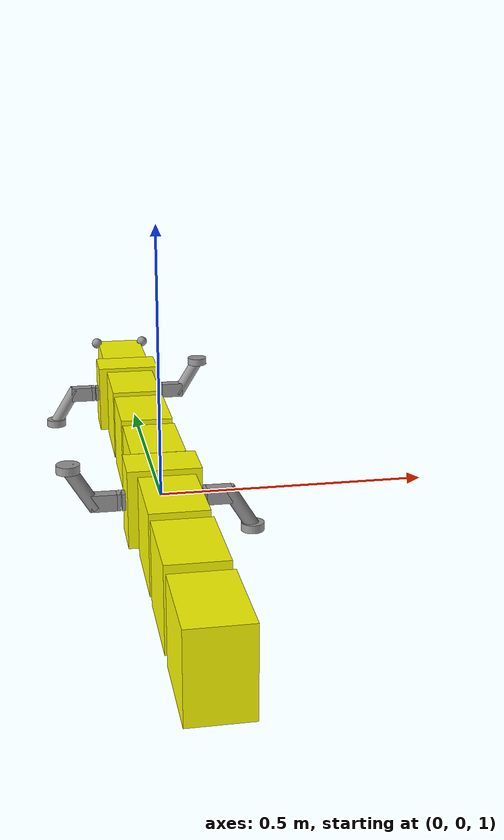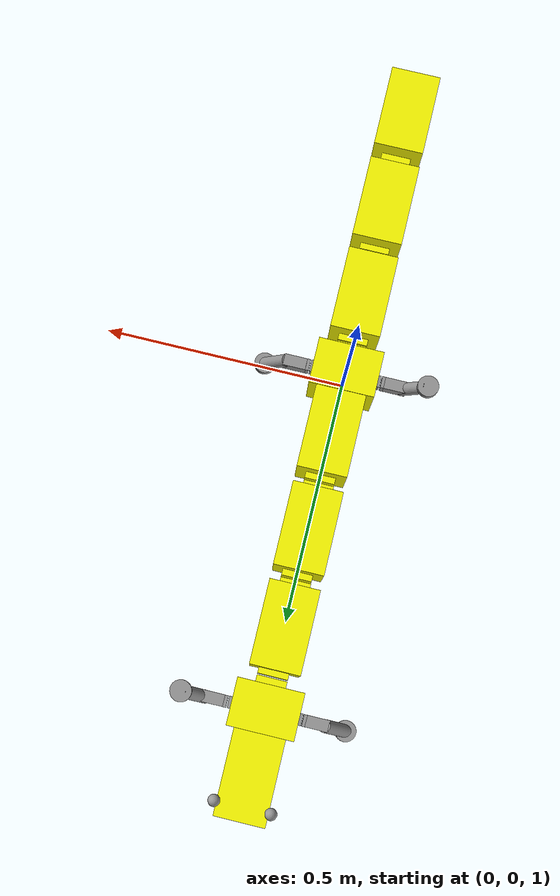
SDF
<?xml version='1.0'?>
<sdf version='1.6'>
  <model name='rrbot'>
    <link name='link_0'>
      <pose frame=''>-4.7e-05 0.811791 1 0 -0 0</pose>
      <inertial>
        <mass>0.5</mass>
        <inertia>
          <ixx>0.00213</ixx>
          <ixy>0</ixy>
          <ixz>0</ixz>
          <iyy>0.00135</iyy>
          <iyz>0</iyz>
          <izz>0.0016</izz>
        </inertia>
        <pose frame=''>0 0 0 0 -0 0</pose>
      </inertial>
      <self_collide>0</self_collide>
      <kinematic>0</kinematic>
      <gravity>1</gravity>
      <visual name='visual'>
        <pose frame=''>0 0 0 0 -0 0</pose>
        <geometry>
          <box>
            <size>0.103506 0.172189 0.147122</size>
          </box>
        </geometry>
        <material>
          <lighting>1</lighting>
          <script>
            <uri>file://media/materials/scripts/gazebo.material</uri>
            <name>Gazebo/Grey</name>
          </script>
          <ambient>1 1 0 0</ambient>
          <diffuse>1 1 0 1</diffuse>
          <specular>0.01 0.01 0.01 1</specular>
          <emissive>0 0 0 1</emissive>
          <shader type='vertex'>
            <normal_map>__default__</normal_map>
          </shader>
        </material>
        <cast_shadows>1</cast_shadows>
        <transparency>0</transparency>
      </visual>
      <collision name='collision'>
        <laser_retro>0</laser_retro>
        <max_contacts>10</max_contacts>
        <pose frame=''>0 0 0 0 -0 0</pose>
        <geometry>
          <box>
            <size>0.103506 0.172189 0.147122</size>
          </box>
        </geometry>
        <surface>
          <friction>
            <ode>
              <mu>0.01</mu>
              <mu2>0.01</mu2>
              <fdir1>0 1 0</fdir1>
              <slip1>0</slip1>
              <slip2>0</slip2>
            </ode>
            <torsional>
              <coefficient>1</coefficient>
              <patch_radius>0</patch_radius>
              <surface_radius>0</surface_radius>
              <use_patch_radius>1</use_patch_radius>
              <ode>
                <slip>0</slip>
              </ode>
            </torsional>
          </friction>
          <bounce>
            <restitution_coefficient>0</restitution_coefficient>
            <threshold>1e+06</threshold>
          </bounce>
          <contact>
            <collide_without_contact>0</collide_without_contact>
            <collide_without_contact_bitmask>1</collide_without_contact_bitmask>
            <collide_bitmask>1</collide_bitmask>
            <ode>
              <soft_cfm>0</soft_cfm>
              <soft_erp>0.2</soft_erp>
              <kp>1e+13</kp>
              <kd>1</kd>
              <max_vel>0.01</max_vel>
              <min_depth>0</min_depth>
            </ode>
            <bullet>
              <split_impulse>1</split_impulse>
              <split_impulse_penetration_threshold>-0.01</split_impulse_penetration_threshold>
              <soft_cfm>0</soft_cfm>
              <soft_erp>0.2</soft_erp>
              <kp>1e+13</kp>
              <kd>1</kd>
            </bullet>
          </contact>
        </surface>
      </collision>
    </link>
    <link name='link_0_0'>
      <pose frame=''>-0.107284 0.681655 1.00213 0 -0 0</pose>
      <inertial>
        <mass>0.04</mass>
        <inertia>
          <ixx>5.3e-06</ixx>
          <ixy>0</ixy>
          <ixz>0</ixz>
          <iyy>1.2e-05</iyy>
          <iyz>0</iyz>
          <izz>1e-05</izz>
        </inertia>
        <pose frame=''>0 0 0 0 -0 0</pose>
      </inertial>
      <self_collide>0</self_collide>
      <kinematic>0</kinematic>
      <visual name='visual'>
        <pose frame=''>0 0 0 0 -0 0</pose>
        <geometry>
          <box>
            <size>0.047498 0.023913 0.031645</size>
          </box>
        </geometry>
        <material>
          <lighting>1</lighting>
          <script>
            <uri>file://media/materials/scripts/gazebo.material</uri>
            <name>Gazebo/Grey</name>
          </script>
          <ambient>0 0 0 1</ambient>
          <diffuse>0 0 0 1</diffuse>
          <specular>0.01 0.01 0.01 1</specular>
          <emissive>0 0 0 1</emissive>
          <shader type='vertex'>
            <normal_map>__default__</normal_map>
          </shader>
        </material>
        <cast_shadows>1</cast_shadows>
        <transparency>0</transparency>
      </visual>
      <collision name='collision'>
        <laser_retro>0</laser_retro>
        <max_contacts>10</max_contacts>
        <pose frame=''>0 0 0 0 -0 0</pose>
        <geometry>
          <box>
            <size>0.047498 0.023913 0.031645</size>
          </box>
        </geometry>
        <surface>
          <friction>
            <ode>
              <mu>1</mu>
              <mu2>1</mu2>
              <fdir1>0 0 0</fdir1>
              <slip1>0</slip1>
              <slip2>0</slip2>
            </ode>
            <torsional>
              <coefficient>1</coefficient>
              <patch_radius>0</patch_radius>
              <surface_radius>0</surface_radius>
              <use_patch_radius>1</use_patch_radius>
              <ode>
                <slip>0</slip>
              </ode>
            </torsional>
          </friction>
          <bounce>
            <restitution_coefficient>0</restitution_coefficient>
            <threshold>1e+06</threshold>
          </bounce>
          <contact>
            <collide_without_contact>0</collide_without_contact>
            <collide_without_contact_bitmask>1</collide_without_contact_bitmask>
            <collide_bitmask>1</collide_bitmask>
            <ode>
              <soft_cfm>0</soft_cfm>
              <soft_erp>0.2</soft_erp>
              <kp>1e+13</kp>
              <kd>1</kd>
              <max_vel>0.01</max_vel>
              <min_depth>0</min_depth>
            </ode>
            <bullet>
              <split_impulse>1</split_impulse>
              <split_impulse_penetration_threshold>-0.01</split_impulse_penetration_threshold>
              <soft_cfm>0</soft_cfm>
              <soft_erp>0.2</soft_erp>
              <kp>1e+13</kp>
              <kd>1</kd>
            </bullet>
          </contact>
        </surface>
      </collision>
    </link>
    <link name='link_0_0_clone'>
      <pose frame=''>0.107284 0.681655 1.00213 0 -0 0</pose>
      <inertial>
        <mass>0.04</mass>
        <inertia>
          <ixx>5.3e-06</ixx>
          <ixy>0</ixy>
          <ixz>0</ixz>
          <iyy>1.2e-05</iyy>
          <iyz>0</iyz>
          <izz>1e-05</izz>
        </inertia>
        <pose frame=''>0 0 0 0 -0 0</pose>
      </inertial>
      <self_collide>0</self_collide>
      <kinematic>0</kinematic>
      <visual name='visual_0'>
        <pose frame=''>0 0 0 0 -0 0</pose>
        <geometry>
          <box>
            <size>0.047498 0.023913 0.031645</size>
          </box>
        </geometry>
        <material>
          <lighting>1</lighting>
          <script>
            <uri>file://media/materials/scripts/gazebo.material</uri>
            <name>Gazebo/Grey</name>
          </script>
          <ambient>0 0 0 1</ambient>
          <diffuse>0 0 0 1</diffuse>
          <specular>0.01 0.01 0.01 1</specular>
          <emissive>0 0 0 1</emissive>
          <shader type='vertex'>
            <normal_map>__default__</normal_map>
          </shader>
        </material>
        <cast_shadows>1</cast_shadows>
        <transparency>0</transparency>
      </visual>
      <collision name='collision'>
        <laser_retro>0</laser_retro>
        <max_contacts>10</max_contacts>
        <pose frame=''>0 0 0 0 -0 0</pose>
        <geometry>
          <box>
            <size>0.047498 0.023913 0.031645</size>
          </box>
        </geometry>
        <surface>
          <friction>
            <ode>
              <mu>1</mu>
              <mu2>1</mu2>
              <fdir1>0 0 0</fdir1>
              <slip1>0</slip1>
              <slip2>0</slip2>
            </ode>
            <torsional>
              <coefficient>1</coefficient>
              <patch_radius>0</patch_radius>
              <surface_radius>0</surface_radius>
              <use_patch_radius>1</use_patch_radius>
              <ode>
                <slip>0</slip>
              </ode>
            </torsional>
          </friction>
          <bounce>
            <restitution_coefficient>0</restitution_coefficient>
            <threshold>1e+06</threshold>
          </bounce>
          <contact>
            <collide_without_contact>0</collide_without_contact>
            <collide_without_contact_bitmask>1</collide_without_contact_bitmask>
            <collide_bitmask>1</collide_bitmask>
            <ode>
              <soft_cfm>0</soft_cfm>
              <soft_erp>0.2</soft_erp>
              <kp>1e+13</kp>
              <kd>1</kd>
              <max_vel>0.01</max_vel>
              <min_depth>0</min_depth>
            </ode>
            <bullet>
              <split_impulse>1</split_impulse>
              <split_impulse_penetration_threshold>-0.01</split_impulse_penetration_threshold>
              <soft_cfm>0</soft_cfm>
              <soft_erp>0.2</soft_erp>
              <kp>1e+13</kp>
              <kd>1</kd>
            </bullet>
          </contact>
        </surface>
      </collision>
    </link>
    <link name='link_0_0_clone_0'>
      <pose frame=''>-0.107284 -0.023563 1.00213 3.6e-05 2.2e-05 -3.6e-05</pose>
      <inertial>
        <mass>0.04</mass>
        <inertia>
          <ixx>5.3e-06</ixx>
          <ixy>0</ixy>
          <ixz>0</ixz>
          <iyy>1.2e-05</iyy>
          <iyz>0</iyz>
          <izz>1e-05</izz>
        </inertia>
        <pose frame=''>0 0 0 0 -0 0</pose>
      </inertial>
      <self_collide>0</self_collide>
      <kinematic>0</kinematic>
      <visual name='visual_0'>
        <pose frame=''>0 0 0 0 -0 0</pose>
        <geometry>
          <box>
            <size>0.047498 0.023913 0.031645</size>
          </box>
        </geometry>
        <material>
          <lighting>1</lighting>
          <script>
            <uri>file://media/materials/scripts/gazebo.material</uri>
            <name>Gazebo/Grey</name>
          </script>
          <ambient>0 0 0 1</ambient>
          <diffuse>0 0 0 1</diffuse>
          <specular>0.01 0.01 0.01 1</specular>
          <emissive>0 0 0 1</emissive>
          <shader type='vertex'>
            <normal_map>__default__</normal_map>
          </shader>
        </material>
        <cast_shadows>1</cast_shadows>
        <transparency>0</transparency>
      </visual>
      <collision name='collision'>
        <laser_retro>0</laser_retro>
        <max_contacts>10</max_contacts>
        <pose frame=''>0 0 0 0 -0 0</pose>
        <geometry>
          <box>
            <size>0.047498 0.023913 0.031645</size>
          </box>
        </geometry>
        <surface>
          <friction>
            <ode>
              <mu>1</mu>
              <mu2>1</mu2>
              <fdir1>0 0 0</fdir1>
              <slip1>0</slip1>
              <slip2>0</slip2>
            </ode>
            <torsional>
              <coefficient>1</coefficient>
              <patch_radius>0</patch_radius>
              <surface_radius>0</surface_radius>
              <use_patch_radius>1</use_patch_radius>
              <ode>
                <slip>0</slip>
              </ode>
            </torsional>
          </friction>
          <bounce>
            <restitution_coefficient>0</restitution_coefficient>
            <threshold>1e+06</threshold>
          </bounce>
          <contact>
            <collide_without_contact>0</collide_without_contact>
            <collide_without_contact_bitmask>1</collide_without_contact_bitmask>
            <collide_bitmask>1</collide_bitmask>
            <ode>
              <soft_cfm>0</soft_cfm>
              <soft_erp>0.2</soft_erp>
              <kp>1e+13</kp>
              <kd>1</kd>
              <max_vel>0.01</max_vel>
              <min_depth>0</min_depth>
            </ode>
            <bullet>
              <split_impulse>1</split_impulse>
              <split_impulse_penetration_threshold>-0.01</split_impulse_penetration_threshold>
              <soft_cfm>0</soft_cfm>
              <soft_erp>0.2</soft_erp>
              <kp>1e+13</kp>
              <kd>1</kd>
            </bullet>
          </contact>
        </surface>
      </collision>
    </link>
    <link name='link_0_0_clone_1'>
      <pose frame=''>0.105506 -0.023563 1.00213 3.6e-05 2.2e-05 -3.6e-05</pose>
      <inertial>
        <mass>0.04</mass>
        <inertia>
          <ixx>5.3e-06</ixx>
          <ixy>0</ixy>
          <ixz>0</ixz>
          <iyy>1.2e-05</iyy>
          <iyz>0</iyz>
          <izz>1e-05</izz>
        </inertia>
        <pose frame=''>0 0 0 0 -0 0</pose>
      </inertial>
      <self_collide>0</self_collide>
      <kinematic>0</kinematic>
      <visual name='visual_0'>
        <pose frame=''>0 0 0 0 -0 0</pose>
        <geometry>
          <box>
            <size>0.047498 0.023913 0.031645</size>
          </box>
        </geometry>
        <material>
          <lighting>1</lighting>
          <script>
            <uri>file://media/materials/scripts/gazebo.material</uri>
            <name>Gazebo/Grey</name>
          </script>
          <ambient>0 0 0 1</ambient>
          <diffuse>0 0 0 1</diffuse>
          <specular>0.01 0.01 0.01 1</specular>
          <emissive>0 0 0 1</emissive>
          <shader type='vertex'>
            <normal_map>__default__</normal_map>
          </shader>
        </material>
        <cast_shadows>1</cast_shadows>
        <transparency>0</transparency>
      </visual>
      <collision name='collision'>
        <laser_retro>0</laser_retro>
        <max_contacts>10</max_contacts>
        <pose frame=''>0 0 0 0 -0 0</pose>
        <geometry>
          <box>
            <size>0.047498 0.023913 0.031645</size>
          </box>
        </geometry>
        <surface>
          <friction>
            <ode>
              <mu>1</mu>
              <mu2>1</mu2>
              <fdir1>0 0 0</fdir1>
              <slip1>0</slip1>
              <slip2>0</slip2>
            </ode>
            <torsional>
              <coefficient>1</coefficient>
              <patch_radius>0</patch_radius>
              <surface_radius>0</surface_radius>
              <use_patch_radius>1</use_patch_radius>
              <ode>
                <slip>0</slip>
              </ode>
            </torsional>
          </friction>
          <bounce>
            <restitution_coefficient>0</restitution_coefficient>
            <threshold>1e+06</threshold>
          </bounce>
          <contact>
            <collide_without_contact>0</collide_without_contact>
            <collide_without_contact_bitmask>1</collide_without_contact_bitmask>
            <collide_bitmask>1</collide_bitmask>
            <ode>
              <soft_cfm>0</soft_cfm>
              <soft_erp>0.2</soft_erp>
              <kp>1e+13</kp>
              <kd>1</kd>
              <max_vel>0.01</max_vel>
              <min_depth>0</min_depth>
            </ode>
            <bullet>
              <split_impulse>1</split_impulse>
              <split_impulse_penetration_threshold>-0.01</split_impulse_penetration_threshold>
              <soft_cfm>0</soft_cfm>
              <soft_erp>0.2</soft_erp>
              <kp>1e+13</kp>
              <kd>1</kd>
            </bullet>
          </contact>
        </surface>
      </collision>
    </link>
    <link name='link_0_0_clone_clone'>
      <pose frame=''>0.071439 0.681684 1.00213 0 -0 0</pose>
      <inertial>
        <mass>0.005</mass>
        <inertia>
          <ixx>6.6e-07</ixx>
          <ixy>0</ixy>
          <ixz>0</ixz>
          <iyy>4.6e-07</iyy>
          <iyz>0</iyz>
          <izz>2.5e-07</izz>
        </inertia>
        <pose frame=''>0 0 0 0 -0 0</pose>
      </inertial>
      <self_collide>0</self_collide>
      <kinematic>0</kinematic>
      <visual name='visual_0'>
        <pose frame=''>0 0 0 0 -0 0</pose>
        <geometry>
          <box>
            <size>0.00666 0.023913 0.031645</size>
          </box>
        </geometry>
        <material>
          <lighting>1</lighting>
          <script>
            <uri>file://media/materials/scripts/gazebo.material</uri>
            <name>Gazebo/Grey</name>
          </script>
          <ambient>0 0 0 1</ambient>
          <diffuse>0 0 0 1</diffuse>
          <specular>0.01 0.01 0.01 1</specular>
          <emissive>0 0 0 1</emissive>
          <shader type='vertex'>
            <normal_map>__default__</normal_map>
          </shader>
        </material>
        <cast_shadows>1</cast_shadows>
        <transparency>0</transparency>
      </visual>
      <collision name='collision'>
        <laser_retro>0</laser_retro>
        <max_contacts>10</max_contacts>
        <pose frame=''>0 0 0 0 -0 0</pose>
        <geometry>
          <box>
            <size>0.00666 0.023913 0.031645</size>
          </box>
        </geometry>
        <surface>
          <friction>
            <ode>
              <mu>0</mu>
              <mu2>0</mu2>
              <fdir1>0 0 0</fdir1>
              <slip1>0</slip1>
              <slip2>0</slip2>
            </ode>
            <torsional>
              <coefficient>1</coefficient>
              <patch_radius>0</patch_radius>
              <surface_radius>0</surface_radius>
              <use_patch_radius>1</use_patch_radius>
              <ode>
                <slip>0</slip>
              </ode>
            </torsional>
          </friction>
          <bounce>
            <restitution_coefficient>0</restitution_coefficient>
            <threshold>1e+06</threshold>
          </bounce>
          <contact>
            <collide_without_contact>0</collide_without_contact>
            <collide_without_contact_bitmask>1</collide_without_contact_bitmask>
            <collide_bitmask>1</collide_bitmask>
            <ode>
              <soft_cfm>0</soft_cfm>
              <soft_erp>0.2</soft_erp>
              <kp>1e+13</kp>
              <kd>1</kd>
              <max_vel>0.01</max_vel>
              <min_depth>0</min_depth>
            </ode>
            <bullet>
              <split_impulse>1</split_impulse>
              <split_impulse_penetration_threshold>-0.01</split_impulse_penetration_threshold>
              <soft_cfm>0</soft_cfm>
              <soft_erp>0.2</soft_erp>
              <kp>1e+13</kp>
              <kd>1</kd>
            </bullet>
          </contact>
        </surface>
      </collision>
    </link>
    <link name='link_0_0_clone_clone_clone'>
      <pose frame=''>0.080726 0.681849 1.00213 0 -0 0</pose>
      <inertial>
        <mass>0.005</mass>
        <inertia>
          <ixx>6.6e-07</ixx>
          <ixy>0</ixy>
          <ixz>0</ixz>
          <iyy>4.6e-07</iyy>
          <iyz>0</iyz>
          <izz>2.5e-07</izz>
        </inertia>
        <pose frame=''>0 0 0 0 -0 0</pose>
      </inertial>
      <self_collide>0</self_collide>
      <kinematic>0</kinematic>
      <visual name='visual_0'>
        <pose frame=''>0 0 0 0 -0 0</pose>
        <geometry>
          <box>
            <size>0.00666 0.023913 0.031645</size>
          </box>
        </geometry>
        <material>
          <lighting>1</lighting>
          <script>
            <uri>file://media/materials/scripts/gazebo.material</uri>
            <name>Gazebo/Grey</name>
          </script>
          <ambient>0 0 0 1</ambient>
          <diffuse>0 0 0 1</diffuse>
          <specular>0.01 0.01 0.01 1</specular>
          <emissive>0 0 0 1</emissive>
          <shader type='vertex'>
            <normal_map>__default__</normal_map>
          </shader>
        </material>
        <cast_shadows>1</cast_shadows>
        <transparency>0</transparency>
      </visual>
      <collision name='collision'>
        <laser_retro>0</laser_retro>
        <max_contacts>10</max_contacts>
        <pose frame=''>0 0 0 0 -0 0</pose>
        <geometry>
          <box>
            <size>0.00666 0.023913 0.031645</size>
          </box>
        </geometry>
        <surface>
          <friction>
            <ode>
              <mu>0</mu>
              <mu2>0</mu2>
              <fdir1>0 0 0</fdir1>
              <slip1>0</slip1>
              <slip2>0</slip2>
            </ode>
            <torsional>
              <coefficient>1</coefficient>
              <patch_radius>0</patch_radius>
              <surface_radius>0</surface_radius>
              <use_patch_radius>1</use_patch_radius>
              <ode>
                <slip>0</slip>
              </ode>
            </torsional>
          </friction>
          <bounce>
            <restitution_coefficient>0</restitution_coefficient>
            <threshold>1e+06</threshold>
          </bounce>
          <contact>
            <collide_without_contact>0</collide_without_contact>
            <collide_without_contact_bitmask>1</collide_without_contact_bitmask>
            <collide_bitmask>1</collide_bitmask>
            <ode>
              <soft_cfm>0</soft_cfm>
              <soft_erp>0.2</soft_erp>
              <kp>1e+13</kp>
              <kd>1</kd>
              <max_vel>0.01</max_vel>
              <min_depth>0</min_depth>
            </ode>
            <bullet>
              <split_impulse>1</split_impulse>
              <split_impulse_penetration_threshold>-0.01</split_impulse_penetration_threshold>
              <soft_cfm>0</soft_cfm>
              <soft_erp>0.2</soft_erp>
              <kp>1e+13</kp>
              <kd>1</kd>
            </bullet>
          </contact>
        </surface>
      </collision>
    </link>
    <link name='link_0_0_clone_clone_clone_0'>
      <pose frame=''>-0.071439 0.681684 1.00213 0 -0 0</pose>
      <inertial>
        <mass>0.005</mass>
        <inertia>
          <ixx>6.6e-07</ixx>
          <ixy>0</ixy>
          <ixz>0</ixz>
          <iyy>4.6e-07</iyy>
          <iyz>0</iyz>
          <izz>2.5e-07</izz>
        </inertia>
        <pose frame=''>0 0 0 0 -0 0</pose>
      </inertial>
      <self_collide>0</self_collide>
      <kinematic>0</kinematic>
      <visual name='visual_0'>
        <pose frame=''>0 0 0 0 -0 0</pose>
        <geometry>
          <box>
            <size>0.00666 0.023913 0.031645</size>
          </box>
        </geometry>
        <material>
          <lighting>1</lighting>
          <script>
            <uri>file://media/materials/scripts/gazebo.material</uri>
            <name>Gazebo/Grey</name>
          </script>
          <ambient>0 0 0 1</ambient>
          <diffuse>0 0 0 1</diffuse>
          <specular>0.01 0.01 0.01 1</specular>
          <emissive>0 0 0 1</emissive>
          <shader type='vertex'>
            <normal_map>__default__</normal_map>
          </shader>
        </material>
        <cast_shadows>1</cast_shadows>
        <transparency>0</transparency>
      </visual>
      <collision name='collision'>
        <laser_retro>0</laser_retro>
        <max_contacts>10</max_contacts>
        <pose frame=''>0 0 0 0 -0 0</pose>
        <geometry>
          <box>
            <size>0.00666 0.023913 0.031645</size>
          </box>
        </geometry>
        <surface>
          <friction>
            <ode>
              <mu>0</mu>
              <mu2>0</mu2>
              <fdir1>0 0 0</fdir1>
              <slip1>0</slip1>
              <slip2>0</slip2>
            </ode>
            <torsional>
              <coefficient>1</coefficient>
              <patch_radius>0</patch_radius>
              <surface_radius>0</surface_radius>
              <use_patch_radius>1</use_patch_radius>
              <ode>
                <slip>0</slip>
              </ode>
            </torsional>
          </friction>
          <bounce>
            <restitution_coefficient>0</restitution_coefficient>
            <threshold>1e+06</threshold>
          </bounce>
          <contact>
            <collide_without_contact>0</collide_without_contact>
            <collide_without_contact_bitmask>1</collide_without_contact_bitmask>
            <collide_bitmask>1</collide_bitmask>
            <ode>
              <soft_cfm>0</soft_cfm>
              <soft_erp>0.2</soft_erp>
              <kp>1e+13</kp>
              <kd>1</kd>
              <max_vel>0.01</max_vel>
              <min_depth>0</min_depth>
            </ode>
            <bullet>
              <split_impulse>1</split_impulse>
              <split_impulse_penetration_threshold>-0.01</split_impulse_penetration_threshold>
              <soft_cfm>0</soft_cfm>
              <soft_erp>0.2</soft_erp>
              <kp>1e+13</kp>
              <kd>1</kd>
            </bullet>
          </contact>
        </surface>
      </collision>
    </link>
    <link name='link_0_0_clone_clone_clone_0_clone'>
      <pose frame=''>-0.080726 0.681849 1.00213 0 -0 0</pose>
      <inertial>
        <mass>0.005</mass>
        <inertia>
          <ixx>6.6e-07</ixx>
          <ixy>0</ixy>
          <ixz>0</ixz>
          <iyy>4.6e-07</iyy>
          <iyz>0</iyz>
          <izz>2.5e-07</izz>
        </inertia>
        <pose frame=''>0 0 0 0 -0 0</pose>
      </inertial>
      <self_collide>0</self_collide>
      <kinematic>0</kinematic>
      <visual name='visual_0'>
        <pose frame=''>0 0 0 0 -0 0</pose>
        <geometry>
          <box>
            <size>0.00666 0.023913 0.031645</size>
          </box>
        </geometry>
        <material>
          <lighting>1</lighting>
          <script>
            <uri>file://media/materials/scripts/gazebo.material</uri>
            <name>Gazebo/Grey</name>
          </script>
          <ambient>0 0 0 1</ambient>
          <diffuse>0 0 0 1</diffuse>
          <specular>0.01 0.01 0.01 1</specular>
          <emissive>0 0 0 1</emissive>
          <shader type='vertex'>
            <normal_map>__default__</normal_map>
          </shader>
        </material>
        <cast_shadows>1</cast_shadows>
        <transparency>0</transparency>
      </visual>
      <collision name='collision'>
        <laser_retro>0</laser_retro>
        <max_contacts>10</max_contacts>
        <pose frame=''>0 0 0 0 -0 0</pose>
        <geometry>
          <box>
            <size>0.00666 0.023913 0.031645</size>
          </box>
        </geometry>
        <surface>
          <friction>
            <ode>
              <mu>0</mu>
              <mu2>0</mu2>
              <fdir1>0 0 0</fdir1>
              <slip1>0</slip1>
              <slip2>0</slip2>
            </ode>
            <torsional>
              <coefficient>1</coefficient>
              <patch_radius>0</patch_radius>
              <surface_radius>0</surface_radius>
              <use_patch_radius>1</use_patch_radius>
              <ode>
                <slip>0</slip>
              </ode>
            </torsional>
          </friction>
          <bounce>
            <restitution_coefficient>0</restitution_coefficient>
            <threshold>1e+06</threshold>
          </bounce>
          <contact>
            <collide_without_contact>0</collide_without_contact>
            <collide_without_contact_bitmask>1</collide_without_contact_bitmask>
            <collide_bitmask>1</collide_bitmask>
            <ode>
              <soft_cfm>0</soft_cfm>
              <soft_erp>0.2</soft_erp>
              <kp>1e+13</kp>
              <kd>1</kd>
              <max_vel>0.01</max_vel>
              <min_depth>0</min_depth>
            </ode>
            <bullet>
              <split_impulse>1</split_impulse>
              <split_impulse_penetration_threshold>-0.01</split_impulse_penetration_threshold>
              <soft_cfm>0</soft_cfm>
              <soft_erp>0.2</soft_erp>
              <kp>1e+13</kp>
              <kd>1</kd>
            </bullet>
          </contact>
        </surface>
      </collision>
    </link>
    <link name='link_0_0_clone_clone_clone_1'>
      <pose frame=''>0.069341 -0.023563 1.00213 0 -0 0</pose>
      <inertial>
        <mass>0.005</mass>
        <inertia>
          <ixx>6.6e-07</ixx>
          <ixy>0</ixy>
          <ixz>0</ixz>
          <iyy>4.6e-07</iyy>
          <iyz>0</iyz>
          <izz>2.5e-07</izz>
        </inertia>
        <pose frame=''>0 0 0 0 -0 0</pose>
      </inertial>
      <self_collide>0</self_collide>
      <kinematic>0</kinematic>
      <visual name='visual_0'>
        <pose frame=''>0 0 0 0 -0 0</pose>
        <geometry>
          <box>
            <size>0.00666 0.023913 0.031645</size>
          </box>
        </geometry>
        <material>
          <lighting>1</lighting>
          <script>
            <uri>file://media/materials/scripts/gazebo.material</uri>
            <name>Gazebo/Grey</name>
          </script>
          <ambient>0 0 0 1</ambient>
          <diffuse>0 0 0 1</diffuse>
          <specular>0.01 0.01 0.01 1</specular>
          <emissive>0 0 0 1</emissive>
          <shader type='vertex'>
            <normal_map>__default__</normal_map>
          </shader>
        </material>
        <cast_shadows>1</cast_shadows>
        <transparency>0</transparency>
      </visual>
      <collision name='collision'>
        <laser_retro>0</laser_retro>
        <max_contacts>10</max_contacts>
        <pose frame=''>0 0 0 0 -0 0</pose>
        <geometry>
          <box>
            <size>0.00666 0.023913 0.031645</size>
          </box>
        </geometry>
        <surface>
          <friction>
            <ode>
              <mu>0</mu>
              <mu2>0</mu2>
              <fdir1>0 0 0</fdir1>
              <slip1>0</slip1>
              <slip2>0</slip2>
            </ode>
            <torsional>
              <coefficient>1</coefficient>
              <patch_radius>0</patch_radius>
              <surface_radius>0</surface_radius>
              <use_patch_radius>1</use_patch_radius>
              <ode>
                <slip>0</slip>
              </ode>
            </torsional>
          </friction>
          <bounce>
            <restitution_coefficient>0</restitution_coefficient>
            <threshold>1e+06</threshold>
          </bounce>
          <contact>
            <collide_without_contact>0</collide_without_contact>
            <collide_without_contact_bitmask>1</collide_without_contact_bitmask>
            <collide_bitmask>1</collide_bitmask>
            <ode>
              <soft_cfm>0</soft_cfm>
              <soft_erp>0.2</soft_erp>
              <kp>1e+13</kp>
              <kd>1</kd>
              <max_vel>0.01</max_vel>
              <min_depth>0</min_depth>
            </ode>
            <bullet>
              <split_impulse>1</split_impulse>
              <split_impulse_penetration_threshold>-0.01</split_impulse_penetration_threshold>
              <soft_cfm>0</soft_cfm>
              <soft_erp>0.2</soft_erp>
              <kp>1e+13</kp>
              <kd>1</kd>
            </bullet>
          </contact>
        </surface>
      </collision>
    </link>
    <link name='link_0_0_clone_clone_clone_2'>
      <pose frame=''>-0.071439 -0.023563 1.00213 0 -0 0</pose>
      <inertial>
        <mass>0.005</mass>
        <inertia>
          <ixx>6.6e-07</ixx>
          <ixy>0</ixy>
          <ixz>0</ixz>
          <iyy>4.6e-07</iyy>
          <iyz>0</iyz>
          <izz>2.5e-07</izz>
        </inertia>
        <pose frame=''>0 0 0 0 -0 0</pose>
      </inertial>
      <self_collide>0</self_collide>
      <kinematic>0</kinematic>
      <visual name='visual_0'>
        <pose frame=''>0 0 0 0 -0 0</pose>
        <geometry>
          <box>
            <size>0.00666 0.023913 0.031645</size>
          </box>
        </geometry>
        <material>
          <lighting>1</lighting>
          <script>
            <uri>file://media/materials/scripts/gazebo.material</uri>
            <name>Gazebo/Grey</name>
          </script>
          <ambient>0 0 0 1</ambient>
          <diffuse>0 0 0 1</diffuse>
          <specular>0.01 0.01 0.01 1</specular>
          <emissive>0 0 0 1</emissive>
          <shader type='vertex'>
            <normal_map>__default__</normal_map>
          </shader>
        </material>
        <cast_shadows>1</cast_shadows>
        <transparency>0</transparency>
      </visual>
      <collision name='collision'>
        <laser_retro>0</laser_retro>
        <max_contacts>10</max_contacts>
        <pose frame=''>0 0 0 0 -0 0</pose>
        <geometry>
          <box>
            <size>0.00666 0.023913 0.031645</size>
          </box>
        </geometry>
        <surface>
          <friction>
            <ode>
              <mu>0</mu>
              <mu2>0</mu2>
              <fdir1>0 0 0</fdir1>
              <slip1>0</slip1>
              <slip2>0</slip2>
            </ode>
            <torsional>
              <coefficient>1</coefficient>
              <patch_radius>0</patch_radius>
              <surface_radius>0</surface_radius>
              <use_patch_radius>1</use_patch_radius>
              <ode>
                <slip>0</slip>
              </ode>
            </torsional>
          </friction>
          <bounce>
            <restitution_coefficient>0</restitution_coefficient>
            <threshold>1e+06</threshold>
          </bounce>
          <contact>
            <collide_without_contact>0</collide_without_contact>
            <collide_without_contact_bitmask>1</collide_without_contact_bitmask>
            <collide_bitmask>1</collide_bitmask>
            <ode>
              <soft_cfm>0</soft_cfm>
              <soft_erp>0.2</soft_erp>
              <kp>1e+13</kp>
              <kd>1</kd>
              <max_vel>0.01</max_vel>
              <min_depth>0</min_depth>
            </ode>
            <bullet>
              <split_impulse>1</split_impulse>
              <split_impulse_penetration_threshold>-0.01</split_impulse_penetration_threshold>
              <soft_cfm>0</soft_cfm>
              <soft_erp>0.2</soft_erp>
              <kp>1e+13</kp>
              <kd>1</kd>
            </bullet>
          </contact>
        </surface>
      </collision>
    </link>
    <link name='link_0_0_clone_clone_clone_3'>
      <pose frame=''>-0.080726 -0.023563 1.00213 0 -0 0</pose>
      <inertial>
        <mass>0.005</mass>
        <inertia>
          <ixx>6.6e-07</ixx>
          <ixy>0</ixy>
          <ixz>0</ixz>
          <iyy>4.6e-07</iyy>
          <iyz>0</iyz>
          <izz>2.5e-07</izz>
        </inertia>
        <pose frame=''>0 0 0 0 -0 0</pose>
      </inertial>
      <self_collide>0</self_collide>
      <kinematic>0</kinematic>
      <visual name='visual_0'>
        <pose frame=''>0 0 0 0 -0 0</pose>
        <geometry>
          <box>
            <size>0.00666 0.023913 0.031645</size>
          </box>
        </geometry>
        <material>
          <lighting>1</lighting>
          <script>
            <uri>file://media/materials/scripts/gazebo.material</uri>
            <name>Gazebo/Grey</name>
          </script>
          <ambient>0 0 0 1</ambient>
          <diffuse>0 0 0 1</diffuse>
          <specular>0.01 0.01 0.01 1</specular>
          <emissive>0 0 0 1</emissive>
          <shader type='vertex'>
            <normal_map>__default__</normal_map>
          </shader>
        </material>
        <cast_shadows>1</cast_shadows>
        <transparency>0</transparency>
      </visual>
      <collision name='collision'>
        <laser_retro>0</laser_retro>
        <max_contacts>10</max_contacts>
        <pose frame=''>0 0 0 0 -0 0</pose>
        <geometry>
          <box>
            <size>0.00666 0.023913 0.031645</size>
          </box>
        </geometry>
        <surface>
          <friction>
            <ode>
              <mu>0</mu>
              <mu2>0</mu2>
              <fdir1>0 0 0</fdir1>
              <slip1>0</slip1>
              <slip2>0</slip2>
            </ode>
            <torsional>
              <coefficient>1</coefficient>
              <patch_radius>0</patch_radius>
              <surface_radius>0</surface_radius>
              <use_patch_radius>1</use_patch_radius>
              <ode>
                <slip>0</slip>
              </ode>
            </torsional>
          </friction>
          <bounce>
            <restitution_coefficient>0</restitution_coefficient>
            <threshold>1e+06</threshold>
          </bounce>
          <contact>
            <collide_without_contact>0</collide_without_contact>
            <collide_without_contact_bitmask>1</collide_without_contact_bitmask>
            <collide_bitmask>1</collide_bitmask>
            <ode>
              <soft_cfm>0</soft_cfm>
              <soft_erp>0.2</soft_erp>
              <kp>1e+13</kp>
              <kd>1</kd>
              <max_vel>0.01</max_vel>
              <min_depth>0</min_depth>
            </ode>
            <bullet>
              <split_impulse>1</split_impulse>
              <split_impulse_penetration_threshold>-0.01</split_impulse_penetration_threshold>
              <soft_cfm>0</soft_cfm>
              <soft_erp>0.2</soft_erp>
              <kp>1e+13</kp>
              <kd>1</kd>
            </bullet>
          </contact>
        </surface>
      </collision>
    </link>
    <link name='link_0_0_clone_clone_clone_clone'>
      <pose frame=''>0.07833 -0.023563 1.00221 0 -0 0</pose>
      <inertial>
        <mass>0.005</mass>
        <inertia>
          <ixx>6.6e-07</ixx>
          <ixy>0</ixy>
          <ixz>0</ixz>
          <iyy>4.6e-07</iyy>
          <iyz>0</iyz>
          <izz>2.5e-07</izz>
        </inertia>
        <pose frame=''>0 0 0 0 -0 0</pose>
      </inertial>
      <self_collide>0</self_collide>
      <kinematic>0</kinematic>
      <visual name='visual_0'>
        <pose frame=''>0 0 0 0 -0 0</pose>
        <geometry>
          <box>
            <size>0.00666 0.023913 0.031645</size>
          </box>
        </geometry>
        <material>
          <lighting>1</lighting>
          <script>
            <uri>file://media/materials/scripts/gazebo.material</uri>
            <name>Gazebo/Grey</name>
          </script>
          <ambient>0 0 0 1</ambient>
          <diffuse>0 0 0 1</diffuse>
          <specular>0.01 0.01 0.01 1</specular>
          <emissive>0 0 0 1</emissive>
          <shader type='vertex'>
            <normal_map>__default__</normal_map>
          </shader>
        </material>
        <cast_shadows>1</cast_shadows>
        <transparency>0</transparency>
      </visual>
      <collision name='collision'>
        <laser_retro>0</laser_retro>
        <max_contacts>10</max_contacts>
        <pose frame=''>0 0 0 0 -0 0</pose>
        <geometry>
          <box>
            <size>0.00666 0.023913 0.031645</size>
          </box>
        </geometry>
        <surface>
          <friction>
            <ode>
              <mu>0</mu>
              <mu2>0</mu2>
              <fdir1>0 0 0</fdir1>
              <slip1>0</slip1>
              <slip2>0</slip2>
            </ode>
            <torsional>
              <coefficient>1</coefficient>
              <patch_radius>0</patch_radius>
              <surface_radius>0</surface_radius>
              <use_patch_radius>1</use_patch_radius>
              <ode>
                <slip>0</slip>
              </ode>
            </torsional>
          </friction>
          <bounce>
            <restitution_coefficient>0</restitution_coefficient>
            <threshold>1e+06</threshold>
          </bounce>
          <contact>
            <collide_without_contact>0</collide_without_contact>
            <collide_without_contact_bitmask>1</collide_without_contact_bitmask>
            <collide_bitmask>1</collide_bitmask>
            <ode>
              <soft_cfm>0</soft_cfm>
              <soft_erp>0.2</soft_erp>
              <kp>1e+13</kp>
              <kd>1</kd>
              <max_vel>0.01</max_vel>
              <min_depth>0</min_depth>
            </ode>
            <bullet>
              <split_impulse>1</split_impulse>
              <split_impulse_penetration_threshold>-0.01</split_impulse_penetration_threshold>
              <soft_cfm>0</soft_cfm>
              <soft_erp>0.2</soft_erp>
              <kp>1e+13</kp>
              <kd>1</kd>
            </bullet>
          </contact>
        </surface>
      </collision>
    </link>
    <link name='link_0_clone'>
      <pose frame=''>-4.7e-05 0.677993 1 0 -0 0</pose>
      <inertial>
        <mass>0.35</mass>
        <inertia>
          <ixx>0.0009</ixx>
          <ixy>0</ixy>
          <ixz>0</ixz>
          <iyy>0.0012</iyy>
          <iyz>0</iyz>
          <izz>0.0008</izz>
        </inertia>
        <pose frame=''>0 0 0 0 -0 0</pose>
      </inertial>
      <self_collide>0</self_collide>
      <kinematic>0</kinematic>
      <gravity>1</gravity>
      <visual name='visual'>
        <pose frame=''>0 0 0 0 -0 0</pose>
        <geometry>
          <box>
            <size>0.13585 0.095615 0.147122</size>
          </box>
        </geometry>
        <material>
          <lighting>1</lighting>
          <script>
            <uri>file://media/materials/scripts/gazebo.material</uri>
            <name>Gazebo/Grey</name>
          </script>
          <ambient>1 1 0 0</ambient>
          <diffuse>1 1 0 1</diffuse>
          <specular>0.01 0.01 0.01 1</specular>
          <emissive>0 0 0 1</emissive>
          <shader type='vertex'>
            <normal_map>__default__</normal_map>
          </shader>
        </material>
        <cast_shadows>1</cast_shadows>
        <transparency>0</transparency>
      </visual>
      <collision name='collision'>
        <laser_retro>0</laser_retro>
        <max_contacts>10</max_contacts>
        <pose frame=''>0 0 0 0 -0 0</pose>
        <geometry>
          <box>
            <size>0.13585 0.095615 0.147122</size>
          </box>
        </geometry>
        <surface>
          <friction>
            <ode>
              <mu>0.01</mu>
              <mu2>0.01</mu2>
              <fdir1>0 1 0</fdir1>
              <slip1>0</slip1>
              <slip2>0</slip2>
            </ode>
            <torsional>
              <coefficient>1</coefficient>
              <patch_radius>0</patch_radius>
              <surface_radius>0</surface_radius>
              <use_patch_radius>1</use_patch_radius>
              <ode>
                <slip>0</slip>
              </ode>
            </torsional>
          </friction>
          <bounce>
            <restitution_coefficient>0</restitution_coefficient>
            <threshold>1e+06</threshold>
          </bounce>
          <contact>
            <collide_without_contact>0</collide_without_contact>
            <collide_without_contact_bitmask>1</collide_without_contact_bitmask>
            <collide_bitmask>1</collide_bitmask>
            <ode>
              <soft_cfm>0</soft_cfm>
              <soft_erp>0.2</soft_erp>
              <kp>1e+13</kp>
              <kd>1</kd>
              <max_vel>0.01</max_vel>
              <min_depth>0</min_depth>
            </ode>
            <bullet>
              <split_impulse>1</split_impulse>
              <split_impulse_penetration_threshold>-0.01</split_impulse_penetration_threshold>
              <soft_cfm>0</soft_cfm>
              <soft_erp>0.2</soft_erp>
              <kp>1e+13</kp>
              <kd>1</kd>
            </bullet>
          </contact>
        </surface>
      </collision>
    </link>
    <link name='link_0_clone_0'>
      <pose frame=''>-4.7e-05 0.514231 1 0 -0 0</pose>
      <inertial>
        <mass>0.4</mass>
        <inertia>
          <ixx>0.0017</ixx>
          <ixy>0</ixy>
          <ixz>0</ixz>
          <iyy>0.0011</iyy>
          <iyz>0</iyz>
          <izz>0.0013</izz>
        </inertia>
        <pose frame=''>0 0 0 0 -0 0</pose>
      </inertial>
      <self_collide>0</self_collide>
      <kinematic>0</kinematic>
      <gravity>1</gravity>
      <visual name='visual'>
        <pose frame=''>0 0 0 0 -0 0</pose>
        <geometry>
          <box>
            <size>0.103506 0.172189 0.147122</size>
          </box>
        </geometry>
        <material>
          <lighting>1</lighting>
          <script>
            <uri>file://media/materials/scripts/gazebo.material</uri>
            <name>Gazebo/Grey</name>
          </script>
          <ambient>1 1 0 0</ambient>
          <diffuse>1 1 0 1</diffuse>
          <specular>0.01 0.01 0.01 1</specular>
          <emissive>0 0 0 1</emissive>
          <shader type='vertex'>
            <normal_map>__default__</normal_map>
          </shader>
        </material>
        <cast_shadows>1</cast_shadows>
        <transparency>0</transparency>
      </visual>
      <collision name='collision'>
        <laser_retro>0</laser_retro>
        <max_contacts>10</max_contacts>
        <pose frame=''>0 0 0 0 -0 0</pose>
        <geometry>
          <box>
            <size>0.103506 0.172189 0.147122</size>
          </box>
        </geometry>
        <surface>
          <friction>
            <ode>
              <mu>0.01</mu>
              <mu2>0.01</mu2>
              <fdir1>0 1 0</fdir1>
              <slip1>0</slip1>
              <slip2>0</slip2>
            </ode>
            <torsional>
              <coefficient>1</coefficient>
              <patch_radius>0</patch_radius>
              <surface_radius>0</surface_radius>
              <use_patch_radius>1</use_patch_radius>
              <ode>
                <slip>0</slip>
              </ode>
            </torsional>
          </friction>
          <bounce>
            <restitution_coefficient>0</restitution_coefficient>
            <threshold>1e+06</threshold>
          </bounce>
          <contact>
            <collide_without_contact>0</collide_without_contact>
            <collide_without_contact_bitmask>1</collide_without_contact_bitmask>
            <collide_bitmask>1</collide_bitmask>
            <ode>
              <soft_cfm>0</soft_cfm>
              <soft_erp>0.2</soft_erp>
              <kp>1e+13</kp>
              <kd>1</kd>
              <max_vel>0.01</max_vel>
              <min_depth>0</min_depth>
            </ode>
            <bullet>
              <split_impulse>1</split_impulse>
              <split_impulse_penetration_threshold>-0.01</split_impulse_penetration_threshold>
              <soft_cfm>0</soft_cfm>
              <soft_erp>0.2</soft_erp>
              <kp>1e+13</kp>
              <kd>1</kd>
            </bullet>
          </contact>
        </surface>
      </collision>
    </link>
    <link name='link_0_clone_1'>
      <pose frame=''>-4.7e-05 0.312921 1 0 -0 0</pose>
      <inertial>
        <mass>0.4</mass>
        <inertia>
          <ixx>0.0017</ixx>
          <ixy>0</ixy>
          <ixz>0</ixz>
          <iyy>0.0011</iyy>
          <iyz>0</iyz>
          <izz>0.0013</izz>
        </inertia>
        <pose frame=''>0 0 0 0 -0 0</pose>
      </inertial>
      <self_collide>0</self_collide>
      <kinematic>0</kinematic>
      <gravity>1</gravity>
      <visual name='visual'>
        <pose frame=''>0 0 0 0 -0 0</pose>
        <geometry>
          <box>
            <size>0.103506 0.172189 0.147122</size>
          </box>
        </geometry>
        <material>
          <lighting>1</lighting>
          <script>
            <uri>file://media/materials/scripts/gazebo.material</uri>
            <name>Gazebo/Grey</name>
          </script>
          <ambient>1 1 0 0</ambient>
          <diffuse>1 1 0 1</diffuse>
          <specular>0.01 0.01 0.01 1</specular>
          <emissive>0 0 0 1</emissive>
          <shader type='vertex'>
            <normal_map>__default__</normal_map>
          </shader>
        </material>
        <cast_shadows>1</cast_shadows>
        <transparency>0</transparency>
      </visual>
      <collision name='collision'>
        <laser_retro>0</laser_retro>
        <max_contacts>10</max_contacts>
        <pose frame=''>0 0 0 0 -0 0</pose>
        <geometry>
          <box>
            <size>0.103506 0.172189 0.147122</size>
          </box>
        </geometry>
        <surface>
          <friction>
            <ode>
              <mu>0.01</mu>
              <mu2>0.01</mu2>
              <fdir1>0 1 0</fdir1>
              <slip1>0</slip1>
              <slip2>0</slip2>
            </ode>
            <torsional>
              <coefficient>1</coefficient>
              <patch_radius>0</patch_radius>
              <surface_radius>0</surface_radius>
              <use_patch_radius>1</use_patch_radius>
              <ode>
                <slip>0</slip>
              </ode>
            </torsional>
          </friction>
          <bounce>
            <restitution_coefficient>0</restitution_coefficient>
            <threshold>1e+06</threshold>
          </bounce>
          <contact>
            <collide_without_contact>0</collide_without_contact>
            <collide_without_contact_bitmask>1</collide_without_contact_bitmask>
            <collide_bitmask>1</collide_bitmask>
            <ode>
              <soft_cfm>0</soft_cfm>
              <soft_erp>0.2</soft_erp>
              <kp>1e+13</kp>
              <kd>1</kd>
              <max_vel>0.01</max_vel>
              <min_depth>0</min_depth>
            </ode>
            <bullet>
              <split_impulse>1</split_impulse>
              <split_impulse_penetration_threshold>-0.01</split_impulse_penetration_threshold>
              <soft_cfm>0</soft_cfm>
              <soft_erp>0.2</soft_erp>
              <kp>1e+13</kp>
              <kd>1</kd>
            </bullet>
          </contact>
        </surface>
      </collision>
    </link>
    <link name='link_0_clone_2'>
      <pose frame=''>-4.7e-05 0.10997 1 0 -0 0</pose>
      <inertial>
        <mass>0.4</mass>
        <inertia>
          <ixx>0.0017</ixx>
          <ixy>0</ixy>
          <ixz>0</ixz>
          <iyy>0.0011</iyy>
          <iyz>0</iyz>
          <izz>0.0013</izz>
        </inertia>
        <pose frame=''>0 0 0 0 -0 0</pose>
      </inertial>
      <self_collide>0</self_collide>
      <kinematic>0</kinematic>
      <gravity>1</gravity>
      <visual name='visual'>
        <pose frame=''>0 0 0 0 -0 0</pose>
        <geometry>
          <box>
            <size>0.103506 0.172189 0.147122</size>
          </box>
        </geometry>
        <material>
          <lighting>1</lighting>
          <script>
            <uri>file://media/materials/scripts/gazebo.material</uri>
            <name>Gazebo/Grey</name>
          </script>
          <ambient>1 1 0 0</ambient>
          <diffuse>1 1 0 1</diffuse>
          <specular>0.01 0.01 0.01 1</specular>
          <emissive>0 0 0 1</emissive>
          <shader type='vertex'>
            <normal_map>__default__</normal_map>
          </shader>
        </material>
        <cast_shadows>1</cast_shadows>
        <transparency>0</transparency>
      </visual>
      <collision name='collision'>
        <laser_retro>0</laser_retro>
        <max_contacts>10</max_contacts>
        <pose frame=''>0 0 0 0 -0 0</pose>
        <geometry>
          <box>
            <size>0.103506 0.172189 0.147122</size>
          </box>
        </geometry>
        <surface>
          <friction>
            <ode>
              <mu>0.01</mu>
              <mu2>0.01</mu2>
              <fdir1>0 1 0</fdir1>
              <slip1>0</slip1>
              <slip2>0</slip2>
            </ode>
            <torsional>
              <coefficient>1</coefficient>
              <patch_radius>0</patch_radius>
              <surface_radius>0</surface_radius>
              <use_patch_radius>1</use_patch_radius>
              <ode>
                <slip>0</slip>
              </ode>
            </torsional>
          </friction>
          <bounce>
            <restitution_coefficient>0</restitution_coefficient>
            <threshold>1e+06</threshold>
          </bounce>
          <contact>
            <collide_without_contact>0</collide_without_contact>
            <collide_without_contact_bitmask>1</collide_without_contact_bitmask>
            <collide_bitmask>1</collide_bitmask>
            <ode>
              <soft_cfm>0</soft_cfm>
              <soft_erp>0.2</soft_erp>
              <kp>1e+13</kp>
              <kd>1</kd>
              <max_vel>0.01</max_vel>
              <min_depth>0</min_depth>
            </ode>
            <bullet>
              <split_impulse>1</split_impulse>
              <split_impulse_penetration_threshold>-0.01</split_impulse_penetration_threshold>
              <soft_cfm>0</soft_cfm>
              <soft_erp>0.2</soft_erp>
              <kp>1e+13</kp>
              <kd>1</kd>
            </bullet>
          </contact>
        </surface>
      </collision>
    </link>
    <link name='link_0_clone_3'>
      <pose frame=''>-4.7e-05 -0.187717 1 0 -0 0</pose>
      <inertial>
        <mass>0.4</mass>
        <inertia>
          <ixx>0.0017</ixx>
          <ixy>0</ixy>
          <ixz>0</ixz>
          <iyy>0.0011</iyy>
          <iyz>0</iyz>
          <izz>0.0013</izz>
        </inertia>
        <pose frame=''>0 0 0 0 -0 0</pose>
      </inertial>
      <self_collide>0</self_collide>
      <kinematic>0</kinematic>
      <gravity>1</gravity>
      <visual name='visual'>
        <pose frame=''>0 0 0 0 -0 0</pose>
        <geometry>
          <box>
            <size>0.103506 0.172189 0.147122</size>
          </box>
        </geometry>
        <material>
          <lighting>1</lighting>
          <script>
            <uri>file://media/materials/scripts/gazebo.material</uri>
            <name>Gazebo/Grey</name>
          </script>
          <ambient>1 1 0 0</ambient>
          <diffuse>1 1 0 1</diffuse>
          <specular>0.01 0.01 0.01 1</specular>
          <emissive>0 0 0 1</emissive>
          <shader type='vertex'>
            <normal_map>__default__</normal_map>
          </shader>
        </material>
        <cast_shadows>1</cast_shadows>
        <transparency>0</transparency>
      </visual>
      <collision name='collision'>
        <laser_retro>0</laser_retro>
        <max_contacts>10</max_contacts>
        <pose frame=''>0 0 0 0 -0 0</pose>
        <geometry>
          <box>
            <size>0.103506 0.172189 0.147122</size>
          </box>
        </geometry>
        <surface>
          <friction>
            <ode>
              <mu>0.01</mu>
              <mu2>0.01</mu2>
              <fdir1>0 1 0</fdir1>
              <slip1>0</slip1>
              <slip2>0</slip2>
            </ode>
            <torsional>
              <coefficient>1</coefficient>
              <patch_radius>0</patch_radius>
              <surface_radius>0</surface_radius>
              <use_patch_radius>1</use_patch_radius>
              <ode>
                <slip>0</slip>
              </ode>
            </torsional>
          </friction>
          <bounce>
            <restitution_coefficient>0</restitution_coefficient>
            <threshold>1e+06</threshold>
          </bounce>
          <contact>
            <collide_without_contact>0</collide_without_contact>
            <collide_without_contact_bitmask>1</collide_without_contact_bitmask>
            <collide_bitmask>1</collide_bitmask>
            <ode>
              <soft_cfm>0</soft_cfm>
              <soft_erp>0.2</soft_erp>
              <kp>1e+13</kp>
              <kd>1</kd>
              <max_vel>0.01</max_vel>
              <min_depth>0</min_depth>
            </ode>
            <bullet>
              <split_impulse>1</split_impulse>
              <split_impulse_penetration_threshold>-0.01</split_impulse_penetration_threshold>
              <soft_cfm>0</soft_cfm>
              <soft_erp>0.2</soft_erp>
              <kp>1e+13</kp>
              <kd>1</kd>
            </bullet>
          </contact>
        </surface>
      </collision>
    </link>
    <link name='link_0_clone_4'>
      <pose frame=''>-4.7e-05 -0.38848 1 0 -0 0</pose>
      <inertial>
        <mass>0.4</mass>
        <inertia>
          <ixx>0.0017</ixx>
          <ixy>0</ixy>
          <ixz>0</ixz>
          <iyy>0.0011</iyy>
          <iyz>0</iyz>
          <izz>0.0013</izz>
        </inertia>
        <pose frame=''>0 0 0 0 -0 0</pose>
      </inertial>
      <self_collide>0</self_collide>
      <kinematic>0</kinematic>
      <gravity>1</gravity>
      <visual name='visual'>
        <pose frame=''>0 0 0 0 -0 0</pose>
        <geometry>
          <box>
            <size>0.103506 0.172189 0.147122</size>
          </box>
        </geometry>
        <material>
          <lighting>1</lighting>
          <script>
            <uri>file://media/materials/scripts/gazebo.material</uri>
            <name>Gazebo/Grey</name>
          </script>
          <ambient>1 1 0 0</ambient>
          <diffuse>1 1 0 1</diffuse>
          <specular>0.01 0.01 0.01 1</specular>
          <emissive>0 0 0 1</emissive>
          <shader type='vertex'>
            <normal_map>__default__</normal_map>
          </shader>
        </material>
        <cast_shadows>1</cast_shadows>
        <transparency>0</transparency>
      </visual>
      <collision name='collision'>
        <laser_retro>0</laser_retro>
        <max_contacts>10</max_contacts>
        <pose frame=''>0 0 0 0 -0 0</pose>
        <geometry>
          <box>
            <size>0.103506 0.172189 0.147122</size>
          </box>
        </geometry>
        <surface>
          <friction>
            <ode>
              <mu>0.01</mu>
              <mu2>0.01</mu2>
              <fdir1>0 1 0</fdir1>
              <slip1>0</slip1>
              <slip2>0</slip2>
            </ode>
            <torsional>
              <coefficient>1</coefficient>
              <patch_radius>0</patch_radius>
              <surface_radius>0</surface_radius>
              <use_patch_radius>1</use_patch_radius>
              <ode>
                <slip>0</slip>
              </ode>
            </torsional>
          </friction>
          <bounce>
            <restitution_coefficient>0</restitution_coefficient>
            <threshold>1e+06</threshold>
          </bounce>
          <contact>
            <collide_without_contact>0</collide_without_contact>
            <collide_without_contact_bitmask>1</collide_without_contact_bitmask>
            <collide_bitmask>1</collide_bitmask>
            <ode>
              <soft_cfm>0</soft_cfm>
              <soft_erp>0.2</soft_erp>
              <kp>1e+13</kp>
              <kd>1</kd>
              <max_vel>0.01</max_vel>
              <min_depth>0</min_depth>
            </ode>
            <bullet>
              <split_impulse>1</split_impulse>
              <split_impulse_penetration_threshold>-0.01</split_impulse_penetration_threshold>
              <soft_cfm>0</soft_cfm>
              <soft_erp>0.2</soft_erp>
              <kp>1e+13</kp>
              <kd>1</kd>
            </bullet>
          </contact>
        </surface>
      </collision>
    </link>
    <link name='link_0_clone_5'>
      <pose frame=''>-4.7e-05 -0.591383 1 0 -0 0</pose>
      <inertial>
        <mass>0.4</mass>
        <inertia>
          <ixx>0.0017</ixx>
          <ixy>0</ixy>
          <ixz>0</ixz>
          <iyy>0.0011</iyy>
          <iyz>0</iyz>
          <izz>0.0013</izz>
        </inertia>
        <pose frame=''>0 0 0 0 -0 0</pose>
      </inertial>
      <self_collide>0</self_collide>
      <kinematic>0</kinematic>
      <gravity>1</gravity>
      <visual name='visual'>
        <pose frame=''>0 0 0 0 -0 0</pose>
        <geometry>
          <box>
            <size>0.103506 0.172189 0.147122</size>
          </box>
        </geometry>
        <material>
          <lighting>1</lighting>
          <script>
            <uri>file://media/materials/scripts/gazebo.material</uri>
            <name>Gazebo/Grey</name>
          </script>
          <ambient>1 1 0 0</ambient>
          <diffuse>1 1 0 1</diffuse>
          <specular>0.01 0.01 0.01 1</specular>
          <emissive>0 0 0 1</emissive>
          <shader type='vertex'>
            <normal_map>__default__</normal_map>
          </shader>
        </material>
        <cast_shadows>1</cast_shadows>
        <transparency>0</transparency>
      </visual>
      <collision name='collision'>
        <laser_retro>0</laser_retro>
        <max_contacts>10</max_contacts>
        <pose frame=''>0 0 0 0 -0 0</pose>
        <geometry>
          <box>
            <size>0.103506 0.172189 0.147122</size>
          </box>
        </geometry>
        <surface>
          <friction>
            <ode>
              <mu>0.01</mu>
              <mu2>0.01</mu2>
              <fdir1>0 1 0</fdir1>
              <slip1>0</slip1>
              <slip2>0</slip2>
            </ode>
            <torsional>
              <coefficient>1</coefficient>
              <patch_radius>0</patch_radius>
              <surface_radius>0</surface_radius>
              <use_patch_radius>1</use_patch_radius>
              <ode>
                <slip>0</slip>
              </ode>
            </torsional>
          </friction>
          <bounce>
            <restitution_coefficient>0</restitution_coefficient>
            <threshold>1e+06</threshold>
          </bounce>
          <contact>
            <collide_without_contact>0</collide_without_contact>
            <collide_without_contact_bitmask>1</collide_without_contact_bitmask>
            <collide_bitmask>1</collide_bitmask>
            <ode>
              <soft_cfm>0</soft_cfm>
              <soft_erp>0.2</soft_erp>
              <kp>1e+13</kp>
              <kd>1</kd>
              <max_vel>0.01</max_vel>
              <min_depth>0</min_depth>
            </ode>
            <bullet>
              <split_impulse>1</split_impulse>
              <split_impulse_penetration_threshold>-0.01</split_impulse_penetration_threshold>
              <soft_cfm>0</soft_cfm>
              <soft_erp>0.2</soft_erp>
              <kp>1e+13</kp>
              <kd>1</kd>
            </bullet>
          </contact>
        </surface>
      </collision>
    </link>
    <link name='link_0_clone_6'>
      <pose frame=''>0.00099 0.623068 0.999998 -3e-06 -1e-06 -0.001241</pose>
      <inertial>
        <mass>0.01</mass>
        <inertia>
          <ixx>2.7e-06</ixx>
          <ixy>0</ixy>
          <ixz>0</ixz>
          <iyy>5.8e-06</iyy>
          <iyz>0</iyz>
          <izz>3.5e-06</izz>
        </inertia>
        <pose frame=''>0 0 0 0 -0 0</pose>
      </inertial>
      <self_collide>0</self_collide>
      <kinematic>0</kinematic>
      <visual name='visual'>
        <pose frame=''>0 0 0 0 -0 0</pose>
        <geometry>
          <box>
            <size>0.061873 0.013761 0.056246</size>
          </box>
        </geometry>
        <material>
          <lighting>1</lighting>
          <script>
            <uri>file://media/materials/scripts/gazebo.material</uri>
            <name>Gazebo/Grey</name>
          </script>
          <ambient>1 1 0 0</ambient>
          <diffuse>1 1 0 1</diffuse>
          <specular>0.01 0.01 0.01 1</specular>
          <emissive>0 0 0 1</emissive>
          <shader type='vertex'>
            <normal_map>__default__</normal_map>
          </shader>
        </material>
        <cast_shadows>1</cast_shadows>
        <transparency>0</transparency>
      </visual>
      <collision name='collision'>
        <laser_retro>0</laser_retro>
        <max_contacts>10</max_contacts>
        <pose frame=''>0 0 0 0 -0 0</pose>
        <geometry>
          <box>
            <size>0.061873 0.013761 0.056246</size>
          </box>
        </geometry>
        <surface>
          <friction>
            <ode>
              <mu>0</mu>
              <mu2>0</mu2>
              <fdir1>0 0 0</fdir1>
              <slip1>0</slip1>
              <slip2>0</slip2>
            </ode>
            <torsional>
              <coefficient>1</coefficient>
              <patch_radius>0</patch_radius>
              <surface_radius>0</surface_radius>
              <use_patch_radius>1</use_patch_radius>
              <ode>
                <slip>0</slip>
              </ode>
            </torsional>
          </friction>
          <bounce>
            <restitution_coefficient>0</restitution_coefficient>
            <threshold>1e+06</threshold>
          </bounce>
          <contact>
            <collide_without_contact>0</collide_without_contact>
            <collide_without_contact_bitmask>1</collide_without_contact_bitmask>
            <collide_bitmask>1</collide_bitmask>
            <ode>
              <soft_cfm>0</soft_cfm>
              <soft_erp>0.2</soft_erp>
              <kp>1e+13</kp>
              <kd>1</kd>
              <max_vel>0.01</max_vel>
              <min_depth>0</min_depth>
            </ode>
            <bullet>
              <split_impulse>1</split_impulse>
              <split_impulse_penetration_threshold>-0.01</split_impulse_penetration_threshold>
              <soft_cfm>0</soft_cfm>
              <soft_erp>0.2</soft_erp>
              <kp>1e+13</kp>
              <kd>1</kd>
            </bullet>
          </contact>
        </surface>
      </collision>
    </link>
    <link name='link_0_clone_6_clone'>
      <pose frame=''>0.000941 0.606003 0.999997 -6e-06 -2e-06 -0.002482</pose>
      <inertial>
        <mass>0.01</mass>
        <inertia>
          <ixx>2.7e-06</ixx>
          <ixy>0</ixy>
          <ixz>0</ixz>
          <iyy>5.8e-06</iyy>
          <iyz>0</iyz>
          <izz>3.5e-06</izz>
        </inertia>
        <pose frame=''>0 0 0 0 -0 0</pose>
      </inertial>
      <self_collide>0</self_collide>
      <kinematic>0</kinematic>
      <visual name='visual'>
        <pose frame=''>0 0 0 0 -0 0</pose>
        <geometry>
          <box>
            <size>0.061873 0.013761 0.056246</size>
          </box>
        </geometry>
        <material>
          <lighting>1</lighting>
          <script>
            <uri>file://media/materials/scripts/gazebo.material</uri>
            <name>Gazebo/Grey</name>
          </script>
          <ambient>1 1 0 0</ambient>
          <diffuse>1 1 0 1</diffuse>
          <specular>0.01 0.01 0.01 1</specular>
          <emissive>0 0 0 1</emissive>
          <shader type='vertex'>
            <normal_map>__default__</normal_map>
          </shader>
        </material>
        <cast_shadows>1</cast_shadows>
        <transparency>0</transparency>
      </visual>
      <collision name='collision'>
        <laser_retro>0</laser_retro>
        <max_contacts>10</max_contacts>
        <pose frame=''>0 0 0 0 -0 0</pose>
        <geometry>
          <box>
            <size>0.061873 0.013761 0.056246</size>
          </box>
        </geometry>
        <surface>
          <friction>
            <ode>
              <mu>0</mu>
              <mu2>0</mu2>
              <fdir1>0 0 0</fdir1>
              <slip1>0</slip1>
              <slip2>0</slip2>
            </ode>
            <torsional>
              <coefficient>1</coefficient>
              <patch_radius>0</patch_radius>
              <surface_radius>0</surface_radius>
              <use_patch_radius>1</use_patch_radius>
              <ode>
                <slip>0</slip>
              </ode>
            </torsional>
          </friction>
          <bounce>
            <restitution_coefficient>0</restitution_coefficient>
            <threshold>1e+06</threshold>
          </bounce>
          <contact>
            <collide_without_contact>0</collide_without_contact>
            <collide_without_contact_bitmask>1</collide_without_contact_bitmask>
            <collide_bitmask>1</collide_bitmask>
            <ode>
              <soft_cfm>0</soft_cfm>
              <soft_erp>0.2</soft_erp>
              <kp>1e+13</kp>
              <kd>1</kd>
              <max_vel>0.01</max_vel>
              <min_depth>0</min_depth>
            </ode>
            <bullet>
              <split_impulse>1</split_impulse>
              <split_impulse_penetration_threshold>-0.01</split_impulse_penetration_threshold>
              <soft_cfm>0</soft_cfm>
              <soft_erp>0.2</soft_erp>
              <kp>1e+13</kp>
              <kd>1</kd>
            </bullet>
          </contact>
        </surface>
      </collision>
    </link>
    <link name='link_0_clone_6_clone_0'>
      <pose frame=''>-4.7e-05 0.423367 1 -6e-06 -2e-06 -0.002482</pose>
      <inertial>
        <mass>0.01</mass>
        <inertia>
          <ixx>2.7e-06</ixx>
          <ixy>0</ixy>
          <ixz>0</ixz>
          <iyy>5.8e-06</iyy>
          <iyz>0</iyz>
          <izz>3.5e-06</izz>
        </inertia>
        <pose frame=''>0 0 0 0 -0 0</pose>
      </inertial>
      <self_collide>0</self_collide>
      <kinematic>0</kinematic>
      <visual name='visual'>
        <pose frame=''>0 0 0 0 -0 0</pose>
        <geometry>
          <box>
            <size>0.061873 0.013761 0.056246</size>
          </box>
        </geometry>
        <material>
          <lighting>1</lighting>
          <script>
            <uri>file://media/materials/scripts/gazebo.material</uri>
            <name>Gazebo/Grey</name>
          </script>
          <ambient>1 1 0 0</ambient>
          <diffuse>1 1 0 1</diffuse>
          <specular>0.01 0.01 0.01 1</specular>
          <emissive>0 0 0 1</emissive>
          <shader type='vertex'>
            <normal_map>__default__</normal_map>
          </shader>
        </material>
        <cast_shadows>1</cast_shadows>
        <transparency>0</transparency>
      </visual>
      <collision name='collision'>
        <laser_retro>0</laser_retro>
        <max_contacts>10</max_contacts>
        <pose frame=''>0 0 0 0 -0 0</pose>
        <geometry>
          <box>
            <size>0.061873 0.013761 0.056246</size>
          </box>
        </geometry>
        <surface>
          <friction>
            <ode>
              <mu>0</mu>
              <mu2>0</mu2>
              <fdir1>0 0 0</fdir1>
              <slip1>0</slip1>
              <slip2>0</slip2>
            </ode>
            <torsional>
              <coefficient>1</coefficient>
              <patch_radius>0</patch_radius>
              <surface_radius>0</surface_radius>
              <use_patch_radius>1</use_patch_radius>
              <ode>
                <slip>0</slip>
              </ode>
            </torsional>
          </friction>
          <bounce>
            <restitution_coefficient>0</restitution_coefficient>
            <threshold>1e+06</threshold>
          </bounce>
          <contact>
            <collide_without_contact>0</collide_without_contact>
            <collide_without_contact_bitmask>1</collide_without_contact_bitmask>
            <collide_bitmask>1</collide_bitmask>
            <ode>
              <soft_cfm>0</soft_cfm>
              <soft_erp>0.2</soft_erp>
              <kp>1e+13</kp>
              <kd>1</kd>
              <max_vel>0.01</max_vel>
              <min_depth>0</min_depth>
            </ode>
            <bullet>
              <split_impulse>1</split_impulse>
              <split_impulse_penetration_threshold>-0.01</split_impulse_penetration_threshold>
              <soft_cfm>0</soft_cfm>
              <soft_erp>0.2</soft_erp>
              <kp>1e+13</kp>
              <kd>1</kd>
            </bullet>
          </contact>
        </surface>
      </collision>
    </link>
    <link name='link_0_clone_6_clone_1'>
      <pose frame=''>-4.7e-05 0.40543 1 -6e-06 -2e-06 -0.002482</pose>
      <inertial>
        <mass>0.01</mass>
        <inertia>
          <ixx>2.7e-06</ixx>
          <ixy>0</ixy>
          <ixz>0</ixz>
          <iyy>5.8e-06</iyy>
          <iyz>0</iyz>
          <izz>3.5e-06</izz>
        </inertia>
        <pose frame=''>0 0 0 0 -0 0</pose>
      </inertial>
      <self_collide>0</self_collide>
      <kinematic>0</kinematic>
      <visual name='visual'>
        <pose frame=''>0 0 0 0 -0 0</pose>
        <geometry>
          <box>
            <size>0.061873 0.013761 0.056246</size>
          </box>
        </geometry>
        <material>
          <lighting>1</lighting>
          <script>
            <uri>file://media/materials/scripts/gazebo.material</uri>
            <name>Gazebo/Grey</name>
          </script>
          <ambient>1 1 0 0</ambient>
          <diffuse>1 1 0 1</diffuse>
          <specular>0.01 0.01 0.01 1</specular>
          <emissive>0 0 0 1</emissive>
          <shader type='vertex'>
            <normal_map>__default__</normal_map>
          </shader>
        </material>
        <cast_shadows>1</cast_shadows>
        <transparency>0</transparency>
      </visual>
      <collision name='collision'>
        <laser_retro>0</laser_retro>
        <max_contacts>10</max_contacts>
        <pose frame=''>0 0 0 0 -0 0</pose>
        <geometry>
          <box>
            <size>0.061873 0.013761 0.056246</size>
          </box>
        </geometry>
        <surface>
          <friction>
            <ode>
              <mu>0</mu>
              <mu2>0</mu2>
              <fdir1>0 0 0</fdir1>
              <slip1>0</slip1>
              <slip2>0</slip2>
            </ode>
            <torsional>
              <coefficient>1</coefficient>
              <patch_radius>0</patch_radius>
              <surface_radius>0</surface_radius>
              <use_patch_radius>1</use_patch_radius>
              <ode>
                <slip>0</slip>
              </ode>
            </torsional>
          </friction>
          <bounce>
            <restitution_coefficient>0</restitution_coefficient>
            <threshold>1e+06</threshold>
          </bounce>
          <contact>
            <collide_without_contact>0</collide_without_contact>
            <collide_without_contact_bitmask>1</collide_without_contact_bitmask>
            <collide_bitmask>1</collide_bitmask>
            <ode>
              <soft_cfm>0</soft_cfm>
              <soft_erp>0.2</soft_erp>
              <kp>1e+13</kp>
              <kd>1</kd>
              <max_vel>0.01</max_vel>
              <min_depth>0</min_depth>
            </ode>
            <bullet>
              <split_impulse>1</split_impulse>
              <split_impulse_penetration_threshold>-0.01</split_impulse_penetration_threshold>
              <soft_cfm>0</soft_cfm>
              <soft_erp>0.2</soft_erp>
              <kp>1e+13</kp>
              <kd>1</kd>
            </bullet>
          </contact>
        </surface>
      </collision>
    </link>
    <link name='link_0_clone_6_clone_2'>
      <pose frame=''>-4.7e-05 0.220346 1 -6e-06 -2e-06 -0.002482</pose>
      <inertial>
        <mass>0.01</mass>
        <inertia>
          <ixx>2.7e-06</ixx>
          <ixy>0</ixy>
          <ixz>0</ixz>
          <iyy>5.8e-06</iyy>
          <iyz>0</iyz>
          <izz>3.5e-06</izz>
        </inertia>
        <pose frame=''>0 0 0 0 -0 0</pose>
      </inertial>
      <self_collide>0</self_collide>
      <kinematic>0</kinematic>
      <visual name='visual'>
        <pose frame=''>0 0 0 0 -0 0</pose>
        <geometry>
          <box>
            <size>0.061873 0.013761 0.056246</size>
          </box>
        </geometry>
        <material>
          <lighting>1</lighting>
          <script>
            <uri>file://media/materials/scripts/gazebo.material</uri>
            <name>Gazebo/Grey</name>
          </script>
          <ambient>1 1 0 0</ambient>
          <diffuse>1 1 0 1</diffuse>
          <specular>0.01 0.01 0.01 1</specular>
          <emissive>0 0 0 1</emissive>
          <shader type='vertex'>
            <normal_map>__default__</normal_map>
          </shader>
        </material>
        <cast_shadows>1</cast_shadows>
        <transparency>0</transparency>
      </visual>
      <collision name='collision'>
        <laser_retro>0</laser_retro>
        <max_contacts>10</max_contacts>
        <pose frame=''>0 0 0 0 -0 0</pose>
        <geometry>
          <box>
            <size>0.061873 0.013761 0.056246</size>
          </box>
        </geometry>
        <surface>
          <friction>
            <ode>
              <mu>0</mu>
              <mu2>0</mu2>
              <fdir1>0 0 0</fdir1>
              <slip1>0</slip1>
              <slip2>0</slip2>
            </ode>
            <torsional>
              <coefficient>1</coefficient>
              <patch_radius>0</patch_radius>
              <surface_radius>0</surface_radius>
              <use_patch_radius>1</use_patch_radius>
              <ode>
                <slip>0</slip>
              </ode>
            </torsional>
          </friction>
          <bounce>
            <restitution_coefficient>0</restitution_coefficient>
            <threshold>1e+06</threshold>
          </bounce>
          <contact>
            <collide_without_contact>0</collide_without_contact>
            <collide_without_contact_bitmask>1</collide_without_contact_bitmask>
            <collide_bitmask>1</collide_bitmask>
            <ode>
              <soft_cfm>0</soft_cfm>
              <soft_erp>0.2</soft_erp>
              <kp>1e+13</kp>
              <kd>1</kd>
              <max_vel>0.01</max_vel>
              <min_depth>0</min_depth>
            </ode>
            <bullet>
              <split_impulse>1</split_impulse>
              <split_impulse_penetration_threshold>-0.01</split_impulse_penetration_threshold>
              <soft_cfm>0</soft_cfm>
              <soft_erp>0.2</soft_erp>
              <kp>1e+13</kp>
              <kd>1</kd>
            </bullet>
          </contact>
        </surface>
      </collision>
    </link>
    <link name='link_0_clone_6_clone_3'>
      <pose frame=''>-4.7e-05 0.202178 1 -6e-06 -2e-06 -0.002482</pose>
      <inertial>
        <mass>0.01</mass>
        <inertia>
          <ixx>2.7e-06</ixx>
          <ixy>0</ixy>
          <ixz>0</ixz>
          <iyy>5.8e-06</iyy>
          <iyz>0</iyz>
          <izz>3.5e-06</izz>
        </inertia>
        <pose frame=''>0 0 0 0 -0 0</pose>
      </inertial>
      <self_collide>0</self_collide>
      <kinematic>0</kinematic>
      <visual name='visual'>
        <pose frame=''>0 0 0 0 -0 0</pose>
        <geometry>
          <box>
            <size>0.061873 0.013761 0.056246</size>
          </box>
        </geometry>
        <material>
          <lighting>1</lighting>
          <script>
            <uri>file://media/materials/scripts/gazebo.material</uri>
            <name>Gazebo/Grey</name>
          </script>
          <ambient>1 1 0 0</ambient>
          <diffuse>1 1 0 1</diffuse>
          <specular>0.01 0.01 0.01 1</specular>
          <emissive>0 0 0 1</emissive>
          <shader type='vertex'>
            <normal_map>__default__</normal_map>
          </shader>
        </material>
        <cast_shadows>1</cast_shadows>
        <transparency>0</transparency>
      </visual>
      <collision name='collision'>
        <laser_retro>0</laser_retro>
        <max_contacts>10</max_contacts>
        <pose frame=''>0 0 0 0 -0 0</pose>
        <geometry>
          <box>
            <size>0.061873 0.013761 0.056246</size>
          </box>
        </geometry>
        <surface>
          <friction>
            <ode>
              <mu>0</mu>
              <mu2>0</mu2>
              <fdir1>0 0 0</fdir1>
              <slip1>0</slip1>
              <slip2>0</slip2>
            </ode>
            <torsional>
              <coefficient>1</coefficient>
              <patch_radius>0</patch_radius>
              <surface_radius>0</surface_radius>
              <use_patch_radius>1</use_patch_radius>
              <ode>
                <slip>0</slip>
              </ode>
            </torsional>
          </friction>
          <bounce>
            <restitution_coefficient>0</restitution_coefficient>
            <threshold>1e+06</threshold>
          </bounce>
          <contact>
            <collide_without_contact>0</collide_without_contact>
            <collide_without_contact_bitmask>1</collide_without_contact_bitmask>
            <collide_bitmask>1</collide_bitmask>
            <ode>
              <soft_cfm>0</soft_cfm>
              <soft_erp>0.2</soft_erp>
              <kp>1e+13</kp>
              <kd>1</kd>
              <max_vel>0.01</max_vel>
              <min_depth>0</min_depth>
            </ode>
            <bullet>
              <split_impulse>1</split_impulse>
              <split_impulse_penetration_threshold>-0.01</split_impulse_penetration_threshold>
              <soft_cfm>0</soft_cfm>
              <soft_erp>0.2</soft_erp>
              <kp>1e+13</kp>
              <kd>1</kd>
            </bullet>
          </contact>
        </surface>
      </collision>
    </link>
    <link name='link_0_clone_6_clone_4'>
      <pose frame=''>-4.7e-05 -0.0792 1 -6e-06 -2e-06 -0.002482</pose>
      <inertial>
        <mass>0.01</mass>
        <inertia>
          <ixx>2.7e-06</ixx>
          <ixy>0</ixy>
          <ixz>0</ixz>
          <iyy>5.8e-06</iyy>
          <iyz>0</iyz>
          <izz>3.5e-06</izz>
        </inertia>
        <pose frame=''>0 0 0 0 -0 0</pose>
      </inertial>
      <self_collide>0</self_collide>
      <kinematic>0</kinematic>
      <visual name='visual'>
        <pose frame=''>0 0 0 0 -0 0</pose>
        <geometry>
          <box>
            <size>0.061873 0.013761 0.056246</size>
          </box>
        </geometry>
        <material>
          <lighting>1</lighting>
          <script>
            <uri>file://media/materials/scripts/gazebo.material</uri>
            <name>Gazebo/Grey</name>
          </script>
          <ambient>1 1 0 0</ambient>
          <diffuse>1 1 0 1</diffuse>
          <specular>0.01 0.01 0.01 1</specular>
          <emissive>0 0 0 1</emissive>
          <shader type='vertex'>
            <normal_map>__default__</normal_map>
          </shader>
        </material>
        <cast_shadows>1</cast_shadows>
        <transparency>0</transparency>
      </visual>
      <collision name='collision'>
        <laser_retro>0</laser_retro>
        <max_contacts>10</max_contacts>
        <pose frame=''>0 0 0 0 -0 0</pose>
        <geometry>
          <box>
            <size>0.061873 0.013761 0.056246</size>
          </box>
        </geometry>
        <surface>
          <friction>
            <ode>
              <mu>0</mu>
              <mu2>0</mu2>
              <fdir1>0 0 0</fdir1>
              <slip1>0</slip1>
              <slip2>0</slip2>
            </ode>
            <torsional>
              <coefficient>1</coefficient>
              <patch_radius>0</patch_radius>
              <surface_radius>0</surface_radius>
              <use_patch_radius>1</use_patch_radius>
              <ode>
                <slip>0</slip>
              </ode>
            </torsional>
          </friction>
          <bounce>
            <restitution_coefficient>0</restitution_coefficient>
            <threshold>1e+06</threshold>
          </bounce>
          <contact>
            <collide_without_contact>0</collide_without_contact>
            <collide_without_contact_bitmask>1</collide_without_contact_bitmask>
            <collide_bitmask>1</collide_bitmask>
            <ode>
              <soft_cfm>0</soft_cfm>
              <soft_erp>0.2</soft_erp>
              <kp>1e+13</kp>
              <kd>1</kd>
              <max_vel>0.01</max_vel>
              <min_depth>0</min_depth>
            </ode>
            <bullet>
              <split_impulse>1</split_impulse>
              <split_impulse_penetration_threshold>-0.01</split_impulse_penetration_threshold>
              <soft_cfm>0</soft_cfm>
              <soft_erp>0.2</soft_erp>
              <kp>1e+13</kp>
              <kd>1</kd>
            </bullet>
          </contact>
        </surface>
      </collision>
    </link>
    <link name='link_0_clone_6_clone_5'>
      <pose frame=''>-4.7e-05 -0.094913 1 -6e-06 -2e-06 -0.002482</pose>
      <inertial>
        <mass>0.01</mass>
        <inertia>
          <ixx>2.7e-06</ixx>
          <ixy>0</ixy>
          <ixz>0</ixz>
          <iyy>5.8e-06</iyy>
          <iyz>0</iyz>
          <izz>3.5e-06</izz>
        </inertia>
        <pose frame=''>0 0 0 0 -0 0</pose>
      </inertial>
      <self_collide>0</self_collide>
      <kinematic>0</kinematic>
      <visual name='visual'>
        <pose frame=''>0 0 0 0 -0 0</pose>
        <geometry>
          <box>
            <size>0.061873 0.013761 0.056246</size>
          </box>
        </geometry>
        <material>
          <lighting>1</lighting>
          <script>
            <uri>file://media/materials/scripts/gazebo.material</uri>
            <name>Gazebo/Grey</name>
          </script>
          <ambient>1 1 0 0</ambient>
          <diffuse>1 1 0 1</diffuse>
          <specular>0.01 0.01 0.01 1</specular>
          <emissive>0 0 0 1</emissive>
          <shader type='vertex'>
            <normal_map>__default__</normal_map>
          </shader>
        </material>
        <cast_shadows>1</cast_shadows>
        <transparency>0</transparency>
      </visual>
      <collision name='collision'>
        <laser_retro>0</laser_retro>
        <max_contacts>10</max_contacts>
        <pose frame=''>0 0 0 0 -0 0</pose>
        <geometry>
          <box>
            <size>0.061873 0.013761 0.056246</size>
          </box>
        </geometry>
        <surface>
          <friction>
            <ode>
              <mu>0</mu>
              <mu2>0</mu2>
              <fdir1>0 0 0</fdir1>
              <slip1>0</slip1>
              <slip2>0</slip2>
            </ode>
            <torsional>
              <coefficient>1</coefficient>
              <patch_radius>0</patch_radius>
              <surface_radius>0</surface_radius>
              <use_patch_radius>1</use_patch_radius>
              <ode>
                <slip>0</slip>
              </ode>
            </torsional>
          </friction>
          <bounce>
            <restitution_coefficient>0</restitution_coefficient>
            <threshold>1e+06</threshold>
          </bounce>
          <contact>
            <collide_without_contact>0</collide_without_contact>
            <collide_without_contact_bitmask>1</collide_without_contact_bitmask>
            <collide_bitmask>1</collide_bitmask>
            <ode>
              <soft_cfm>0</soft_cfm>
              <soft_erp>0.2</soft_erp>
              <kp>1e+13</kp>
              <kd>1</kd>
              <max_vel>0.01</max_vel>
              <min_depth>0</min_depth>
            </ode>
            <bullet>
              <split_impulse>1</split_impulse>
              <split_impulse_penetration_threshold>-0.01</split_impulse_penetration_threshold>
              <soft_cfm>0</soft_cfm>
              <soft_erp>0.2</soft_erp>
              <kp>1e+13</kp>
              <kd>1</kd>
            </bullet>
          </contact>
        </surface>
      </collision>
    </link>
    <link name='link_0_clone_6_clone_6'>
      <pose frame=''>-4.7e-05 -0.280501 1 -6e-06 -2e-06 -0.002482</pose>
      <inertial>
        <mass>0.01</mass>
        <inertia>
          <ixx>2.7e-06</ixx>
          <ixy>0</ixy>
          <ixz>0</ixz>
          <iyy>5.8e-06</iyy>
          <iyz>0</iyz>
          <izz>3.5e-06</izz>
        </inertia>
        <pose frame=''>0 0 0 0 -0 0</pose>
      </inertial>
      <self_collide>0</self_collide>
      <kinematic>0</kinematic>
      <visual name='visual'>
        <pose frame=''>0 0 0 0 -0 0</pose>
        <geometry>
          <box>
            <size>0.061873 0.013761 0.056246</size>
          </box>
        </geometry>
        <material>
          <lighting>1</lighting>
          <script>
            <uri>file://media/materials/scripts/gazebo.material</uri>
            <name>Gazebo/Grey</name>
          </script>
          <ambient>1 1 0 0</ambient>
          <diffuse>1 1 0 1</diffuse>
          <specular>0.01 0.01 0.01 1</specular>
          <emissive>0 0 0 1</emissive>
          <shader type='vertex'>
            <normal_map>__default__</normal_map>
          </shader>
        </material>
        <cast_shadows>1</cast_shadows>
        <transparency>0</transparency>
      </visual>
      <collision name='collision'>
        <laser_retro>0</laser_retro>
        <max_contacts>10</max_contacts>
        <pose frame=''>0 0 0 0 -0 0</pose>
        <geometry>
          <box>
            <size>0.061873 0.013761 0.056246</size>
          </box>
        </geometry>
        <surface>
          <friction>
            <ode>
              <mu>0</mu>
              <mu2>0</mu2>
              <fdir1>0 0 0</fdir1>
              <slip1>0</slip1>
              <slip2>0</slip2>
            </ode>
            <torsional>
              <coefficient>1</coefficient>
              <patch_radius>0</patch_radius>
              <surface_radius>0</surface_radius>
              <use_patch_radius>1</use_patch_radius>
              <ode>
                <slip>0</slip>
              </ode>
            </torsional>
          </friction>
          <bounce>
            <restitution_coefficient>0</restitution_coefficient>
            <threshold>1e+06</threshold>
          </bounce>
          <contact>
            <collide_without_contact>0</collide_without_contact>
            <collide_without_contact_bitmask>1</collide_without_contact_bitmask>
            <collide_bitmask>1</collide_bitmask>
            <ode>
              <soft_cfm>0</soft_cfm>
              <soft_erp>0.2</soft_erp>
              <kp>1e+13</kp>
              <kd>1</kd>
              <max_vel>0.01</max_vel>
              <min_depth>0</min_depth>
            </ode>
            <bullet>
              <split_impulse>1</split_impulse>
              <split_impulse_penetration_threshold>-0.01</split_impulse_penetration_threshold>
              <soft_cfm>0</soft_cfm>
              <soft_erp>0.2</soft_erp>
              <kp>1e+13</kp>
              <kd>1</kd>
            </bullet>
          </contact>
        </surface>
      </collision>
    </link>
    <link name='link_0_clone_6_clone_7'>
      <pose frame=''>-4.7e-05 -0.296252 1 -6e-06 -2e-06 -0.002482</pose>
      <inertial>
        <mass>0.01</mass>
        <inertia>
          <ixx>2.7e-06</ixx>
          <ixy>0</ixy>
          <ixz>0</ixz>
          <iyy>5.8e-06</iyy>
          <iyz>0</iyz>
          <izz>3.5e-06</izz>
        </inertia>
        <pose frame=''>0 0 0 0 -0 0</pose>
      </inertial>
      <self_collide>0</self_collide>
      <kinematic>0</kinematic>
      <visual name='visual'>
        <pose frame=''>0 0 0 0 -0 0</pose>
        <geometry>
          <box>
            <size>0.061873 0.013761 0.056246</size>
          </box>
        </geometry>
        <material>
          <lighting>1</lighting>
          <script>
            <uri>file://media/materials/scripts/gazebo.material</uri>
            <name>Gazebo/Grey</name>
          </script>
          <ambient>1 1 0 0</ambient>
          <diffuse>1 1 0 1</diffuse>
          <specular>0.01 0.01 0.01 1</specular>
          <emissive>0 0 0 1</emissive>
          <shader type='vertex'>
            <normal_map>__default__</normal_map>
          </shader>
        </material>
        <cast_shadows>1</cast_shadows>
        <transparency>0</transparency>
      </visual>
      <collision name='collision'>
        <laser_retro>0</laser_retro>
        <max_contacts>10</max_contacts>
        <pose frame=''>0 0 0 0 -0 0</pose>
        <geometry>
          <box>
            <size>0.061873 0.013761 0.056246</size>
          </box>
        </geometry>
        <surface>
          <friction>
            <ode>
              <mu>0</mu>
              <mu2>0</mu2>
              <fdir1>0 0 0</fdir1>
              <slip1>0</slip1>
              <slip2>0</slip2>
            </ode>
            <torsional>
              <coefficient>1</coefficient>
              <patch_radius>0</patch_radius>
              <surface_radius>0</surface_radius>
              <use_patch_radius>1</use_patch_radius>
              <ode>
                <slip>0</slip>
              </ode>
            </torsional>
          </friction>
          <bounce>
            <restitution_coefficient>0</restitution_coefficient>
            <threshold>1e+06</threshold>
          </bounce>
          <contact>
            <collide_without_contact>0</collide_without_contact>
            <collide_without_contact_bitmask>1</collide_without_contact_bitmask>
            <collide_bitmask>1</collide_bitmask>
            <ode>
              <soft_cfm>0</soft_cfm>
              <soft_erp>0.2</soft_erp>
              <kp>1e+13</kp>
              <kd>1</kd>
              <max_vel>0.01</max_vel>
              <min_depth>0</min_depth>
            </ode>
            <bullet>
              <split_impulse>1</split_impulse>
              <split_impulse_penetration_threshold>-0.01</split_impulse_penetration_threshold>
              <soft_cfm>0</soft_cfm>
              <soft_erp>0.2</soft_erp>
              <kp>1e+13</kp>
              <kd>1</kd>
            </bullet>
          </contact>
        </surface>
      </collision>
    </link>
    <link name='link_0_clone_6_clone_8'>
      <pose frame=''>-4.7e-05 -0.481182 1 -6e-06 -2e-06 -0.002482</pose>
      <inertial>
        <mass>0.01</mass>
        <inertia>
          <ixx>2.7e-06</ixx>
          <ixy>0</ixy>
          <ixz>0</ixz>
          <iyy>5.8e-06</iyy>
          <iyz>0</iyz>
          <izz>3.5e-06</izz>
        </inertia>
        <pose frame=''>0 0 0 0 -0 0</pose>
      </inertial>
      <self_collide>0</self_collide>
      <kinematic>0</kinematic>
      <visual name='visual'>
        <pose frame=''>0 0 0 0 -0 0</pose>
        <geometry>
          <box>
            <size>0.061873 0.013761 0.056246</size>
          </box>
        </geometry>
        <material>
          <lighting>1</lighting>
          <script>
            <uri>file://media/materials/scripts/gazebo.material</uri>
            <name>Gazebo/Grey</name>
          </script>
          <ambient>1 1 0 0</ambient>
          <diffuse>1 1 0 1</diffuse>
          <specular>0.01 0.01 0.01 1</specular>
          <emissive>0 0 0 1</emissive>
          <shader type='vertex'>
            <normal_map>__default__</normal_map>
          </shader>
        </material>
        <cast_shadows>1</cast_shadows>
        <transparency>0</transparency>
      </visual>
      <collision name='collision'>
        <laser_retro>0</laser_retro>
        <max_contacts>10</max_contacts>
        <pose frame=''>0 0 0 0 -0 0</pose>
        <geometry>
          <box>
            <size>0.061873 0.013761 0.056246</size>
          </box>
        </geometry>
        <surface>
          <friction>
            <ode>
              <mu>0</mu>
              <mu2>0</mu2>
              <fdir1>0 0 0</fdir1>
              <slip1>0</slip1>
              <slip2>0</slip2>
            </ode>
            <torsional>
              <coefficient>1</coefficient>
              <patch_radius>0</patch_radius>
              <surface_radius>0</surface_radius>
              <use_patch_radius>1</use_patch_radius>
              <ode>
                <slip>0</slip>
              </ode>
            </torsional>
          </friction>
          <bounce>
            <restitution_coefficient>0</restitution_coefficient>
            <threshold>1e+06</threshold>
          </bounce>
          <contact>
            <collide_without_contact>0</collide_without_contact>
            <collide_without_contact_bitmask>1</collide_without_contact_bitmask>
            <collide_bitmask>1</collide_bitmask>
            <ode>
              <soft_cfm>0</soft_cfm>
              <soft_erp>0.2</soft_erp>
              <kp>1e+13</kp>
              <kd>1</kd>
              <max_vel>0.01</max_vel>
              <min_depth>0</min_depth>
            </ode>
            <bullet>
              <split_impulse>1</split_impulse>
              <split_impulse_penetration_threshold>-0.01</split_impulse_penetration_threshold>
              <soft_cfm>0</soft_cfm>
              <soft_erp>0.2</soft_erp>
              <kp>1e+13</kp>
              <kd>1</kd>
            </bullet>
          </contact>
        </surface>
      </collision>
    </link>
    <link name='link_0_clone_6_clone_9'>
      <pose frame=''>-4.7e-05 -0.49872 1 -6e-06 -2e-06 -0.002482</pose>
      <inertial>
        <mass>0.01</mass>
        <inertia>
          <ixx>2.7e-06</ixx>
          <ixy>0</ixy>
          <ixz>0</ixz>
          <iyy>5.8e-06</iyy>
          <iyz>0</iyz>
          <izz>3.5e-06</izz>
        </inertia>
        <pose frame=''>0 0 0 0 -0 0</pose>
      </inertial>
      <self_collide>0</self_collide>
      <kinematic>0</kinematic>
      <visual name='visual'>
        <pose frame=''>0 0 0 0 -0 0</pose>
        <geometry>
          <box>
            <size>0.061873 0.013761 0.056246</size>
          </box>
        </geometry>
        <material>
          <lighting>1</lighting>
          <script>
            <uri>file://media/materials/scripts/gazebo.material</uri>
            <name>Gazebo/Grey</name>
          </script>
          <ambient>1 1 0 0</ambient>
          <diffuse>1 1 0 1</diffuse>
          <specular>0.01 0.01 0.01 1</specular>
          <emissive>0 0 0 1</emissive>
          <shader type='vertex'>
            <normal_map>__default__</normal_map>
          </shader>
        </material>
        <cast_shadows>1</cast_shadows>
        <transparency>0</transparency>
      </visual>
      <collision name='collision'>
        <laser_retro>0</laser_retro>
        <max_contacts>10</max_contacts>
        <pose frame=''>0 0 0 0 -0 0</pose>
        <geometry>
          <box>
            <size>0.061873 0.013761 0.056246</size>
          </box>
        </geometry>
        <surface>
          <friction>
            <ode>
              <mu>0</mu>
              <mu2>0</mu2>
              <fdir1>0 0 0</fdir1>
              <slip1>0</slip1>
              <slip2>0</slip2>
            </ode>
            <torsional>
              <coefficient>1</coefficient>
              <patch_radius>0</patch_radius>
              <surface_radius>0</surface_radius>
              <use_patch_radius>1</use_patch_radius>
              <ode>
                <slip>0</slip>
              </ode>
            </torsional>
          </friction>
          <bounce>
            <restitution_coefficient>0</restitution_coefficient>
            <threshold>1e+06</threshold>
          </bounce>
          <contact>
            <collide_without_contact>0</collide_without_contact>
            <collide_without_contact_bitmask>1</collide_without_contact_bitmask>
            <collide_bitmask>1</collide_bitmask>
            <ode>
              <soft_cfm>0</soft_cfm>
              <soft_erp>0.2</soft_erp>
              <kp>1e+13</kp>
              <kd>1</kd>
              <max_vel>0.01</max_vel>
              <min_depth>0</min_depth>
            </ode>
            <bullet>
              <split_impulse>1</split_impulse>
              <split_impulse_penetration_threshold>-0.01</split_impulse_penetration_threshold>
              <soft_cfm>0</soft_cfm>
              <soft_erp>0.2</soft_erp>
              <kp>1e+13</kp>
              <kd>1</kd>
            </bullet>
          </contact>
        </surface>
      </collision>
    </link>
    <link name='link_0_clone_clone'>
      <pose frame=''>-4.7e-05 -0.024346 1 1.8e-05 1.1e-05 -1.8e-05</pose>
      <inertial>
        <mass>0.35</mass>
        <inertia>
          <ixx>0.0009</ixx>
          <ixy>0</ixy>
          <ixz>0</ixz>
          <iyy>0.0012</iyy>
          <iyz>0</iyz>
          <izz>0.0008</izz>
        </inertia>
        <pose frame=''>0 0 0 0 -0 0</pose>
      </inertial>
      <self_collide>0</self_collide>
      <kinematic>0</kinematic>
      <gravity>1</gravity>
      <visual name='visual'>
        <pose frame=''>0 0 0 0 -0 0</pose>
        <geometry>
          <box>
            <size>0.13585 0.095615 0.147122</size>
          </box>
        </geometry>
        <material>
          <lighting>1</lighting>
          <script>
            <uri>file://media/materials/scripts/gazebo.material</uri>
            <name>Gazebo/Grey</name>
          </script>
          <ambient>1 1 0 0</ambient>
          <diffuse>1 1 0 1</diffuse>
          <specular>0.01 0.01 0.01 1</specular>
          <emissive>0 0 0 1</emissive>
          <shader type='vertex'>
            <normal_map>__default__</normal_map>
          </shader>
        </material>
        <cast_shadows>1</cast_shadows>
        <transparency>0</transparency>
      </visual>
      <collision name='collision'>
        <laser_retro>0</laser_retro>
        <max_contacts>10</max_contacts>
        <pose frame=''>0 0 0 0 -0 0</pose>
        <geometry>
          <box>
            <size>0.13585 0.095615 0.147122</size>
          </box>
        </geometry>
        <surface>
          <friction>
            <ode>
              <mu>0.01</mu>
              <mu2>0.01</mu2>
              <fdir1>0 1 0</fdir1>
              <slip1>0</slip1>
              <slip2>0</slip2>
            </ode>
            <torsional>
              <coefficient>1</coefficient>
              <patch_radius>0</patch_radius>
              <surface_radius>0</surface_radius>
              <use_patch_radius>1</use_patch_radius>
              <ode>
                <slip>0</slip>
              </ode>
            </torsional>
          </friction>
          <bounce>
            <restitution_coefficient>0</restitution_coefficient>
            <threshold>1e+06</threshold>
          </bounce>
          <contact>
            <collide_without_contact>0</collide_without_contact>
            <collide_without_contact_bitmask>1</collide_without_contact_bitmask>
            <collide_bitmask>1</collide_bitmask>
            <ode>
              <soft_cfm>0</soft_cfm>
              <soft_erp>0.2</soft_erp>
              <kp>1e+13</kp>
              <kd>1</kd>
              <max_vel>0.01</max_vel>
              <min_depth>0</min_depth>
            </ode>
            <bullet>
              <split_impulse>1</split_impulse>
              <split_impulse_penetration_threshold>-0.01</split_impulse_penetration_threshold>
              <soft_cfm>0</soft_cfm>
              <soft_erp>0.2</soft_erp>
              <kp>1e+13</kp>
              <kd>1</kd>
            </bullet>
          </contact>
        </surface>
      </collision>
    </link>
    <link name='link_2_clone'>
      <pose frame=''>0.169267 0.68271 1.06978 0 -0 0</pose>
      <inertial>
        <mass>0.02</mass>
        <inertia>
          <ixx>1.7e-06</ixx>
          <ixy>0</ixy>
          <ixz>0</ixz>
          <iyy>1.7e-06</iyy>
          <iyz>0</iyz>
          <izz>1.7e-06</izz>
        </inertia>
        <pose frame=''>0 0 0 0 -0 0</pose>
      </inertial>
      <self_collide>0</self_collide>
      <kinematic>0</kinematic>
      <visual name='visual'>
        <pose frame=''>0 0 0 0 -0 0</pose>
        <geometry>
          <cylinder>
            <radius>0.0217706</radius>
            <length>0.0158511</length>
          </cylinder>
        </geometry>
        <material>
          <lighting>1</lighting>
          <script>
            <uri>file://media/materials/scripts/gazebo.material</uri>
            <name>Gazebo/Grey</name>
          </script>
          <ambient>0 0 0 1</ambient>
          <diffuse>0 0 0 1</diffuse>
          <specular>0.01 0.01 0.01 1</specular>
          <emissive>0 0 0 1</emissive>
          <shader type='vertex'>
            <normal_map>__default__</normal_map>
          </shader>
        </material>
        <cast_shadows>1</cast_shadows>
        <transparency>0</transparency>
      </visual>
      <collision name='collision'>
        <laser_retro>0</laser_retro>
        <max_contacts>10</max_contacts>
        <pose frame=''>0 0 0 0 -0 0</pose>
        <geometry>
          <cylinder>
            <radius>0.021771</radius>
            <length>0.015619</length>
          </cylinder>
        </geometry>
        <surface>
          <friction>
            <ode>
              <mu>1.5</mu>
              <mu2>1.5</mu2>
              <fdir1>0 1 0</fdir1>
              <slip1>0</slip1>
              <slip2>0</slip2>
            </ode>
            <torsional>
              <coefficient>1</coefficient>
              <patch_radius>0</patch_radius>
              <surface_radius>0</surface_radius>
              <use_patch_radius>1</use_patch_radius>
              <ode>
                <slip>0</slip>
              </ode>
            </torsional>
          </friction>
          <bounce>
            <restitution_coefficient>0</restitution_coefficient>
            <threshold>1e+06</threshold>
          </bounce>
          <contact>
            <collide_without_contact>0</collide_without_contact>
            <collide_without_contact_bitmask>1</collide_without_contact_bitmask>
            <collide_bitmask>1</collide_bitmask>
            <ode>
              <soft_cfm>0</soft_cfm>
              <soft_erp>0.2</soft_erp>
              <kp>1e+13</kp>
              <kd>1</kd>
              <max_vel>0.1</max_vel>
              <min_depth>0.003</min_depth>
            </ode>
            <bullet>
              <split_impulse>1</split_impulse>
              <split_impulse_penetration_threshold>-0.01</split_impulse_penetration_threshold>
              <soft_cfm>0</soft_cfm>
              <soft_erp>0.2</soft_erp>
              <kp>1e+13</kp>
              <kd>1</kd>
            </bullet>
          </contact>
        </surface>
      </collision>
    </link>
    <link name='link_2_clone_1'>
      <pose frame=''>0.146283 0.68271 1.03112 0 0.548987 0</pose>
      <inertial>
        <mass>0.03</mass>
        <inertia>
          <ixx>0.0001</ixx>
          <ixy>0</ixy>
          <ixz>0</ixz>
          <iyy>0.0001</iyy>
          <iyz>0</iyz>
          <izz>0.0001</izz>
        </inertia>
        <pose frame=''>0 0 0 0 -0 0</pose>
      </inertial>
      <self_collide>0</self_collide>
      <kinematic>0</kinematic>
      <visual name='visual'>
        <pose frame=''>0 0 0 0 -0 0</pose>
        <geometry>
          <cylinder>
            <radius>0.013308</radius>
            <length>0.093809</length>
          </cylinder>
        </geometry>
        <material>
          <lighting>1</lighting>
          <script>
            <uri>file://media/materials/scripts/gazebo.material</uri>
            <name>Gazebo/Grey</name>
          </script>
          <ambient>0 0 0 1</ambient>
          <diffuse>0 0 0 1</diffuse>
          <specular>0.01 0.01 0.01 1</specular>
          <emissive>0 0 0 1</emissive>
          <shader type='vertex'>
            <normal_map>__default__</normal_map>
          </shader>
        </material>
        <cast_shadows>1</cast_shadows>
        <transparency>0</transparency>
      </visual>
      <collision name='collision'>
        <laser_retro>0</laser_retro>
        <max_contacts>10</max_contacts>
        <pose frame=''>0 0 0 0 -0 0</pose>
        <geometry>
          <cylinder>
            <radius>0.013308</radius>
            <length>0.092439</length>
          </cylinder>
        </geometry>
        <surface>
          <friction>
            <ode>
              <mu>1</mu>
              <mu2>1</mu2>
              <fdir1>0 0 0</fdir1>
              <slip1>0</slip1>
              <slip2>0</slip2>
            </ode>
            <torsional>
              <coefficient>1</coefficient>
              <patch_radius>0</patch_radius>
              <surface_radius>0</surface_radius>
              <use_patch_radius>1</use_patch_radius>
              <ode>
                <slip>0</slip>
              </ode>
            </torsional>
          </friction>
          <bounce>
            <restitution_coefficient>0</restitution_coefficient>
            <threshold>1e+06</threshold>
          </bounce>
          <contact>
            <collide_without_contact>0</collide_without_contact>
            <collide_without_contact_bitmask>1</collide_without_contact_bitmask>
            <collide_bitmask>1</collide_bitmask>
            <ode>
              <soft_cfm>0</soft_cfm>
              <soft_erp>0.2</soft_erp>
              <kp>1e+13</kp>
              <kd>1</kd>
              <max_vel>0.01</max_vel>
              <min_depth>0</min_depth>
            </ode>
            <bullet>
              <split_impulse>1</split_impulse>
              <split_impulse_penetration_threshold>-0.01</split_impulse_penetration_threshold>
              <soft_cfm>0</soft_cfm>
              <soft_erp>0.2</soft_erp>
              <kp>1e+13</kp>
              <kd>1</kd>
            </bullet>
          </contact>
        </surface>
      </collision>
    </link>
    <link name='link_2_clone_1_clone'>
      <pose frame=''>-0.146283 0.68271 0.973145 0 0.548987 0</pose>
      <inertial>
        <mass>0.03</mass>
        <inertia>
          <ixx>0.0001</ixx>
          <ixy>0</ixy>
          <ixz>0</ixz>
          <iyy>0.0001</iyy>
          <iyz>0</iyz>
          <izz>0.0001</izz>
        </inertia>
        <pose frame=''>0 0 0 0 -0 0</pose>
      </inertial>
      <self_collide>0</self_collide>
      <kinematic>0</kinematic>
      <visual name='visual'>
        <pose frame=''>0 0 0 0 -0 0</pose>
        <geometry>
          <cylinder>
            <radius>0.013308</radius>
            <length>0.093809</length>
          </cylinder>
        </geometry>
        <material>
          <lighting>1</lighting>
          <script>
            <uri>file://media/materials/scripts/gazebo.material</uri>
            <name>Gazebo/Grey</name>
          </script>
          <ambient>0 0 0 1</ambient>
          <diffuse>0 0 0 1</diffuse>
          <specular>0.01 0.01 0.01 1</specular>
          <emissive>0 0 0 1</emissive>
          <shader type='vertex'>
            <normal_map>__default__</normal_map>
          </shader>
        </material>
        <cast_shadows>1</cast_shadows>
        <transparency>0</transparency>
      </visual>
      <collision name='collision'>
        <laser_retro>0</laser_retro>
        <max_contacts>10</max_contacts>
        <pose frame=''>0 0 0 0 -0 0</pose>
        <geometry>
          <cylinder>
            <radius>0.013308</radius>
            <length>0.092439</length>
          </cylinder>
        </geometry>
        <surface>
          <friction>
            <ode>
              <mu>1</mu>
              <mu2>1</mu2>
              <fdir1>0 0 0</fdir1>
              <slip1>0</slip1>
              <slip2>0</slip2>
            </ode>
            <torsional>
              <coefficient>1</coefficient>
              <patch_radius>0</patch_radius>
              <surface_radius>0</surface_radius>
              <use_patch_radius>1</use_patch_radius>
              <ode>
                <slip>0</slip>
              </ode>
            </torsional>
          </friction>
          <bounce>
            <restitution_coefficient>0</restitution_coefficient>
            <threshold>1e+06</threshold>
          </bounce>
          <contact>
            <collide_without_contact>0</collide_without_contact>
            <collide_without_contact_bitmask>1</collide_without_contact_bitmask>
            <collide_bitmask>1</collide_bitmask>
            <ode>
              <soft_cfm>0</soft_cfm>
              <soft_erp>0.2</soft_erp>
              <kp>1e+13</kp>
              <kd>1</kd>
              <max_vel>0.01</max_vel>
              <min_depth>0</min_depth>
            </ode>
            <bullet>
              <split_impulse>1</split_impulse>
              <split_impulse_penetration_threshold>-0.01</split_impulse_penetration_threshold>
              <soft_cfm>0</soft_cfm>
              <soft_erp>0.2</soft_erp>
              <kp>1e+13</kp>
              <kd>1</kd>
            </bullet>
          </contact>
        </surface>
      </collision>
    </link>
    <link name='link_2_clone_1_clone_0'>
      <pose frame=''>0.146283 -0.023563 0.973145 0 -0.548994 0</pose>
      <inertial>
        <mass>0.03</mass>
        <inertia>
          <ixx>0.0001</ixx>
          <ixy>0</ixy>
          <ixz>0</ixz>
          <iyy>0.0001</iyy>
          <iyz>0</iyz>
          <izz>0.0001</izz>
        </inertia>
        <pose frame=''>0 0 0 0 -0 0</pose>
      </inertial>
      <self_collide>0</self_collide>
      <kinematic>0</kinematic>
      <visual name='visual'>
        <pose frame=''>0 0 0 0 -0 0</pose>
        <geometry>
          <cylinder>
            <radius>0.013308</radius>
            <length>0.093809</length>
          </cylinder>
        </geometry>
        <material>
          <lighting>1</lighting>
          <script>
            <uri>file://media/materials/scripts/gazebo.material</uri>
            <name>Gazebo/Grey</name>
          </script>
          <ambient>0 0 0 1</ambient>
          <diffuse>0 0 0 1</diffuse>
          <specular>0.01 0.01 0.01 1</specular>
          <emissive>0 0 0 1</emissive>
          <shader type='vertex'>
            <normal_map>__default__</normal_map>
          </shader>
        </material>
        <cast_shadows>1</cast_shadows>
        <transparency>0</transparency>
      </visual>
      <collision name='collision'>
        <laser_retro>0</laser_retro>
        <max_contacts>10</max_contacts>
        <pose frame=''>0 0 0 0 -0 0</pose>
        <geometry>
          <cylinder>
            <radius>0.013308</radius>
            <length>0.092439</length>
          </cylinder>
        </geometry>
        <surface>
          <friction>
            <ode>
              <mu>1</mu>
              <mu2>1</mu2>
              <fdir1>0 0 0</fdir1>
              <slip1>0</slip1>
              <slip2>0</slip2>
            </ode>
            <torsional>
              <coefficient>1</coefficient>
              <patch_radius>0</patch_radius>
              <surface_radius>0</surface_radius>
              <use_patch_radius>1</use_patch_radius>
              <ode>
                <slip>0</slip>
              </ode>
            </torsional>
          </friction>
          <bounce>
            <restitution_coefficient>0</restitution_coefficient>
            <threshold>1e+06</threshold>
          </bounce>
          <contact>
            <collide_without_contact>0</collide_without_contact>
            <collide_without_contact_bitmask>1</collide_without_contact_bitmask>
            <collide_bitmask>1</collide_bitmask>
            <ode>
              <soft_cfm>0</soft_cfm>
              <soft_erp>0.2</soft_erp>
              <kp>1e+13</kp>
              <kd>1</kd>
              <max_vel>0.01</max_vel>
              <min_depth>0</min_depth>
            </ode>
            <bullet>
              <split_impulse>1</split_impulse>
              <split_impulse_penetration_threshold>-0.01</split_impulse_penetration_threshold>
              <soft_cfm>0</soft_cfm>
              <soft_erp>0.2</soft_erp>
              <kp>1e+13</kp>
              <kd>1</kd>
            </bullet>
          </contact>
        </surface>
      </collision>
    </link>
    <link name='link_2_clone_1_clone_0_clone'>
      <pose frame=''>-0.146283 -0.023563 1.03112 0 -0.548994 0</pose>
      <inertial>
        <mass>0.03</mass>
        <inertia>
          <ixx>0.0001</ixx>
          <ixy>0</ixy>
          <ixz>0</ixz>
          <iyy>0.0001</iyy>
          <iyz>0</iyz>
          <izz>0.0001</izz>
        </inertia>
        <pose frame=''>0 0 0 0 -0 0</pose>
      </inertial>
      <self_collide>0</self_collide>
      <kinematic>0</kinematic>
      <visual name='visual'>
        <pose frame=''>0 0 0 0 -0 0</pose>
        <geometry>
          <cylinder>
            <radius>0.013308</radius>
            <length>0.093809</length>
          </cylinder>
        </geometry>
        <material>
          <lighting>1</lighting>
          <script>
            <uri>file://media/materials/scripts/gazebo.material</uri>
            <name>Gazebo/Grey</name>
          </script>
          <ambient>0 0 0 1</ambient>
          <diffuse>0 0 0 1</diffuse>
          <specular>0.01 0.01 0.01 1</specular>
          <emissive>0 0 0 1</emissive>
          <shader type='vertex'>
            <normal_map>__default__</normal_map>
          </shader>
        </material>
        <cast_shadows>1</cast_shadows>
        <transparency>0</transparency>
      </visual>
      <collision name='collision'>
        <laser_retro>0</laser_retro>
        <max_contacts>10</max_contacts>
        <pose frame=''>0 0 0 0 -0 0</pose>
        <geometry>
          <cylinder>
            <radius>0.013308</radius>
            <length>0.092439</length>
          </cylinder>
        </geometry>
        <surface>
          <friction>
            <ode>
              <mu>1</mu>
              <mu2>1</mu2>
              <fdir1>0 0 0</fdir1>
              <slip1>0</slip1>
              <slip2>0</slip2>
            </ode>
            <torsional>
              <coefficient>1</coefficient>
              <patch_radius>0</patch_radius>
              <surface_radius>0</surface_radius>
              <use_patch_radius>1</use_patch_radius>
              <ode>
                <slip>0</slip>
              </ode>
            </torsional>
          </friction>
          <bounce>
            <restitution_coefficient>0</restitution_coefficient>
            <threshold>1e+06</threshold>
          </bounce>
          <contact>
            <collide_without_contact>0</collide_without_contact>
            <collide_without_contact_bitmask>1</collide_without_contact_bitmask>
            <collide_bitmask>1</collide_bitmask>
            <ode>
              <soft_cfm>0</soft_cfm>
              <soft_erp>0.2</soft_erp>
              <kp>1e+13</kp>
              <kd>1</kd>
              <max_vel>0.01</max_vel>
              <min_depth>0</min_depth>
            </ode>
            <bullet>
              <split_impulse>1</split_impulse>
              <split_impulse_penetration_threshold>-0.01</split_impulse_penetration_threshold>
              <soft_cfm>0</soft_cfm>
              <soft_erp>0.2</soft_erp>
              <kp>1e+13</kp>
              <kd>1</kd>
            </bullet>
          </contact>
        </surface>
      </collision>
    </link>
    <link name='link_2_clone_clone'>
      <pose frame=''>-0.169267 0.68271 0.93448 0 -0 0</pose>
      <inertial>
        <mass>0.02</mass>
        <inertia>
          <ixx>1.7e-06</ixx>
          <ixy>0</ixy>
          <ixz>0</ixz>
          <iyy>1.7e-06</iyy>
          <iyz>0</iyz>
          <izz>1.7e-06</izz>
        </inertia>
        <pose frame=''>0 0 0 0 -0 0</pose>
      </inertial>
      <self_collide>0</self_collide>
      <kinematic>0</kinematic>
      <visual name='visual'>
        <pose frame=''>0 0 0 0 -0 0</pose>
        <geometry>
          <cylinder>
            <radius>0.0217706</radius>
            <length>0.0158511</length>
          </cylinder>
        </geometry>
        <material>
          <lighting>1</lighting>
          <script>
            <uri>file://media/materials/scripts/gazebo.material</uri>
            <name>Gazebo/Grey</name>
          </script>
          <ambient>0 0 0 1</ambient>
          <diffuse>0 0 0 1</diffuse>
          <specular>0.01 0.01 0.01 1</specular>
          <emissive>0 0 0 1</emissive>
          <shader type='vertex'>
            <normal_map>__default__</normal_map>
          </shader>
        </material>
        <cast_shadows>1</cast_shadows>
        <transparency>0</transparency>
      </visual>
      <collision name='collision'>
        <laser_retro>0</laser_retro>
        <max_contacts>10</max_contacts>
        <pose frame=''>0 0 0 0 -0 0</pose>
        <geometry>
          <cylinder>
            <radius>0.021771</radius>
            <length>0.015619</length>
          </cylinder>
        </geometry>
        <surface>
          <friction>
            <ode>
              <mu>1.5</mu>
              <mu2>1.5</mu2>
              <fdir1>0 1 0</fdir1>
              <slip1>0</slip1>
              <slip2>0</slip2>
            </ode>
            <torsional>
              <coefficient>1</coefficient>
              <patch_radius>0</patch_radius>
              <surface_radius>0</surface_radius>
              <use_patch_radius>1</use_patch_radius>
              <ode>
                <slip>0</slip>
              </ode>
            </torsional>
          </friction>
          <bounce>
            <restitution_coefficient>0</restitution_coefficient>
            <threshold>1e+06</threshold>
          </bounce>
          <contact>
            <collide_without_contact>0</collide_without_contact>
            <collide_without_contact_bitmask>1</collide_without_contact_bitmask>
            <collide_bitmask>1</collide_bitmask>
            <ode>
              <soft_cfm>0</soft_cfm>
              <soft_erp>0.2</soft_erp>
              <kp>1e+13</kp>
              <kd>1</kd>
              <max_vel>0.1</max_vel>
              <min_depth>0.003</min_depth>
            </ode>
            <bullet>
              <split_impulse>1</split_impulse>
              <split_impulse_penetration_threshold>-0.01</split_impulse_penetration_threshold>
              <soft_cfm>0</soft_cfm>
              <soft_erp>0.2</soft_erp>
              <kp>1e+13</kp>
              <kd>1</kd>
            </bullet>
          </contact>
        </surface>
      </collision>
    </link>
    <link name='link_2_clone_clone_0'>
      <pose frame=''>0.169267 -0.023563 0.93448 0 -0 0</pose>
      <inertial>
        <mass>0.02</mass>
        <inertia>
          <ixx>1.7e-06</ixx>
          <ixy>0</ixy>
          <ixz>0</ixz>
          <iyy>1.7e-06</iyy>
          <iyz>0</iyz>
          <izz>1.7e-06</izz>
        </inertia>
        <pose frame=''>0 0 0 0 -0 0</pose>
      </inertial>
      <self_collide>0</self_collide>
      <kinematic>0</kinematic>
      <visual name='visual'>
        <pose frame=''>0 0 0 0 -0 0</pose>
        <geometry>
          <cylinder>
            <radius>0.0217706</radius>
            <length>0.0158511</length>
          </cylinder>
        </geometry>
        <material>
          <lighting>1</lighting>
          <script>
            <uri>file://media/materials/scripts/gazebo.material</uri>
            <name>Gazebo/Grey</name>
          </script>
          <ambient>0 0 0 1</ambient>
          <diffuse>0 0 0 1</diffuse>
          <specular>0.01 0.01 0.01 1</specular>
          <emissive>0 0 0 1</emissive>
          <shader type='vertex'>
            <normal_map>__default__</normal_map>
          </shader>
        </material>
        <cast_shadows>1</cast_shadows>
        <transparency>0</transparency>
      </visual>
      <collision name='collision'>
        <laser_retro>0</laser_retro>
        <max_contacts>10</max_contacts>
        <pose frame=''>0 0 0 0 -0 0</pose>
        <geometry>
          <cylinder>
            <radius>0.021771</radius>
            <length>0.015619</length>
          </cylinder>
        </geometry>
        <surface>
          <friction>
            <ode>
              <mu>1.5</mu>
              <mu2>1.5</mu2>
              <fdir1>0 1 0</fdir1>
              <slip1>0</slip1>
              <slip2>0</slip2>
            </ode>
            <torsional>
              <coefficient>1</coefficient>
              <patch_radius>0</patch_radius>
              <surface_radius>0</surface_radius>
              <use_patch_radius>1</use_patch_radius>
              <ode>
                <slip>0</slip>
              </ode>
            </torsional>
          </friction>
          <bounce>
            <restitution_coefficient>0</restitution_coefficient>
            <threshold>1e+06</threshold>
          </bounce>
          <contact>
            <collide_without_contact>0</collide_without_contact>
            <collide_without_contact_bitmask>1</collide_without_contact_bitmask>
            <collide_bitmask>1</collide_bitmask>
            <ode>
              <soft_cfm>0</soft_cfm>
              <soft_erp>0.2</soft_erp>
              <kp>1e+13</kp>
              <kd>1</kd>
              <max_vel>0.1</max_vel>
              <min_depth>0.003</min_depth>
            </ode>
            <bullet>
              <split_impulse>1</split_impulse>
              <split_impulse_penetration_threshold>-0.01</split_impulse_penetration_threshold>
              <soft_cfm>0</soft_cfm>
              <soft_erp>0.2</soft_erp>
              <kp>1e+13</kp>
              <kd>1</kd>
            </bullet>
          </contact>
        </surface>
      </collision>
    </link>
    <link name='link_2_clone_clone_0_clone'>
      <pose frame=''>-0.169267 -0.023563 1.06978 0 -0 0</pose>
      <inertial>
        <mass>0.02</mass>
        <inertia>
          <ixx>1.7e-06</ixx>
          <ixy>0</ixy>
          <ixz>0</ixz>
          <iyy>1.7e-06</iyy>
          <iyz>0</iyz>
          <izz>1.7e-06</izz>
        </inertia>
        <pose frame=''>0 0 0 0 -0 0</pose>
      </inertial>
      <self_collide>0</self_collide>
      <kinematic>0</kinematic>
      <visual name='visual'>
        <pose frame=''>0 0 0 0 -0 0</pose>
        <geometry>
          <cylinder>
            <radius>0.0217706</radius>
            <length>0.0158511</length>
          </cylinder>
        </geometry>
        <material>
          <lighting>1</lighting>
          <script>
            <uri>file://media/materials/scripts/gazebo.material</uri>
            <name>Gazebo/Grey</name>
          </script>
          <ambient>0 0 0 1</ambient>
          <diffuse>0 0 0 1</diffuse>
          <specular>0.01 0.01 0.01 1</specular>
          <emissive>0 0 0 1</emissive>
          <shader type='vertex'>
            <normal_map>__default__</normal_map>
          </shader>
        </material>
        <cast_shadows>1</cast_shadows>
        <transparency>0</transparency>
      </visual>
      <collision name='collision'>
        <laser_retro>0</laser_retro>
        <max_contacts>10</max_contacts>
        <pose frame=''>0 0 0 0 -0 0</pose>
        <geometry>
          <cylinder>
            <radius>0.021771</radius>
            <length>0.015619</length>
          </cylinder>
        </geometry>
        <surface>
          <friction>
            <ode>
              <mu>1.5</mu>
              <mu2>1.5</mu2>
              <fdir1>0 1 0</fdir1>
              <slip1>0</slip1>
              <slip2>0</slip2>
            </ode>
            <torsional>
              <coefficient>1</coefficient>
              <patch_radius>0</patch_radius>
              <surface_radius>0</surface_radius>
              <use_patch_radius>1</use_patch_radius>
              <ode>
                <slip>0</slip>
              </ode>
            </torsional>
          </friction>
          <bounce>
            <restitution_coefficient>0</restitution_coefficient>
            <threshold>1e+06</threshold>
          </bounce>
          <contact>
            <collide_without_contact>0</collide_without_contact>
            <collide_without_contact_bitmask>1</collide_without_contact_bitmask>
            <collide_bitmask>1</collide_bitmask>
            <ode>
              <soft_cfm>0</soft_cfm>
              <soft_erp>0.2</soft_erp>
              <kp>1e+13</kp>
              <kd>1</kd>
              <max_vel>0.1</max_vel>
              <min_depth>0.003</min_depth>
            </ode>
            <bullet>
              <split_impulse>1</split_impulse>
              <split_impulse_penetration_threshold>-0.01</split_impulse_penetration_threshold>
              <soft_cfm>0</soft_cfm>
              <soft_erp>0.2</soft_erp>
              <kp>1e+13</kp>
              <kd>1</kd>
            </bullet>
          </contact>
        </surface>
      </collision>
    </link>
    <link name='link_3'>
      <pose frame=''>-0.056366 0.869284 1.07634 1.8e-05 1.1e-05 -1.8e-05</pose>
      <inertial>
        <mass>1.433e-05</mass>
        <inertia>
          <ixx>0</ixx>
          <ixy>0</ixy>
          <ixz>0</ixz>
          <iyy>0</iyy>
          <iyz>0</iyz>
          <izz>0</izz>
        </inertia>
        <pose frame=''>0 0 0 0 -0 0</pose>
      </inertial>
      <self_collide>0</self_collide>
      <kinematic>0</kinematic>
      <visual name='visual'>
        <pose frame=''>0 0 0 0 -0 0</pose>
        <geometry>
          <sphere>
            <radius>0.0121437</radius>
          </sphere>
        </geometry>
        <material>
          <lighting>1</lighting>
          <script>
            <uri>file://media/materials/scripts/gazebo.material</uri>
            <name>Gazebo/Grey</name>
          </script>
          <ambient>0 0 0 1</ambient>
          <diffuse>0 0 0 1</diffuse>
          <specular>0.01 0.01 0.01 1</specular>
          <emissive>0 0 0 1</emissive>
          <shader type='vertex'>
            <normal_map>__default__</normal_map>
          </shader>
        </material>
        <cast_shadows>1</cast_shadows>
        <transparency>0</transparency>
      </visual>
      <collision name='collision'>
        <laser_retro>0</laser_retro>
        <max_contacts>10</max_contacts>
        <pose frame=''>0 0 0 0 -0 0</pose>
        <geometry>
          <sphere>
            <radius>0.012144</radius>
          </sphere>
        </geometry>
        <surface>
          <friction>
            <ode>
              <mu>1</mu>
              <mu2>1</mu2>
              <fdir1>0 0 0</fdir1>
              <slip1>0</slip1>
              <slip2>0</slip2>
            </ode>
            <torsional>
              <coefficient>1</coefficient>
              <patch_radius>0</patch_radius>
              <surface_radius>0</surface_radius>
              <use_patch_radius>1</use_patch_radius>
              <ode>
                <slip>0</slip>
              </ode>
            </torsional>
          </friction>
          <bounce>
            <restitution_coefficient>0</restitution_coefficient>
            <threshold>1e+06</threshold>
          </bounce>
          <contact>
            <collide_without_contact>0</collide_without_contact>
            <collide_without_contact_bitmask>1</collide_without_contact_bitmask>
            <collide_bitmask>1</collide_bitmask>
            <ode>
              <soft_cfm>0</soft_cfm>
              <soft_erp>0.2</soft_erp>
              <kp>1e+13</kp>
              <kd>1</kd>
              <max_vel>0.01</max_vel>
              <min_depth>0</min_depth>
            </ode>
            <bullet>
              <split_impulse>1</split_impulse>
              <split_impulse_penetration_threshold>-0.01</split_impulse_penetration_threshold>
              <soft_cfm>0</soft_cfm>
              <soft_erp>0.2</soft_erp>
              <kp>1e+13</kp>
              <kd>1</kd>
            </bullet>
          </contact>
        </surface>
      </collision>
    </link>
    <link name='link_3_clone'>
      <pose frame=''>0.056366 0.869284 1.07634 3.6e-05 2.2e-05 -3.6e-05</pose>
      <inertial>
        <mass>1.433e-05</mass>
        <inertia>
          <ixx>0</ixx>
          <ixy>0</ixy>
          <ixz>0</ixz>
          <iyy>0</iyy>
          <iyz>0</iyz>
          <izz>0</izz>
        </inertia>
        <pose frame=''>0 0 0 0 -0 0</pose>
      </inertial>
      <self_collide>0</self_collide>
      <kinematic>0</kinematic>
      <visual name='visual'>
        <pose frame=''>0 0 0 0 -0 0</pose>
        <geometry>
          <sphere>
            <radius>0.0121437</radius>
          </sphere>
        </geometry>
        <material>
          <lighting>1</lighting>
          <script>
            <uri>file://media/materials/scripts/gazebo.material</uri>
            <name>Gazebo/Grey</name>
          </script>
          <ambient>0 0 0 1</ambient>
          <diffuse>0 0 0 1</diffuse>
          <specular>0.01 0.01 0.01 1</specular>
          <emissive>0 0 0 1</emissive>
          <shader type='vertex'>
            <normal_map>__default__</normal_map>
          </shader>
        </material>
        <cast_shadows>1</cast_shadows>
        <transparency>0</transparency>
      </visual>
      <collision name='collision'>
        <laser_retro>0</laser_retro>
        <max_contacts>10</max_contacts>
        <pose frame=''>0 0 0 0 -0 0</pose>
        <geometry>
          <sphere>
            <radius>0.012144</radius>
          </sphere>
        </geometry>
        <surface>
          <friction>
            <ode>
              <mu>1</mu>
              <mu2>1</mu2>
              <fdir1>0 0 0</fdir1>
              <slip1>0</slip1>
              <slip2>0</slip2>
            </ode>
            <torsional>
              <coefficient>1</coefficient>
              <patch_radius>0</patch_radius>
              <surface_radius>0</surface_radius>
              <use_patch_radius>1</use_patch_radius>
              <ode>
                <slip>0</slip>
              </ode>
            </torsional>
          </friction>
          <bounce>
            <restitution_coefficient>0</restitution_coefficient>
            <threshold>1e+06</threshold>
          </bounce>
          <contact>
            <collide_without_contact>0</collide_without_contact>
            <collide_without_contact_bitmask>1</collide_without_contact_bitmask>
            <collide_bitmask>1</collide_bitmask>
            <ode>
              <soft_cfm>0</soft_cfm>
              <soft_erp>0.2</soft_erp>
              <kp>1e+13</kp>
              <kd>1</kd>
              <max_vel>0.01</max_vel>
              <min_depth>0</min_depth>
            </ode>
            <bullet>
              <split_impulse>1</split_impulse>
              <split_impulse_penetration_threshold>-0.01</split_impulse_penetration_threshold>
              <soft_cfm>0</soft_cfm>
              <soft_erp>0.2</soft_erp>
              <kp>1e+13</kp>
              <kd>1</kd>
            </bullet>
          </contact>
        </surface>
      </collision>
    </link>
    <joint name='link_0_0_JOINT_2' type='fixed'>
      <parent>link_0_0</parent>
      <child>link_2_clone_1_clone</child>
      <pose frame=''>0 0 0 0 -0 0</pose>
      <physics>
        <ode>
          <limit>
            <cfm>0</cfm>
            <erp>0.2</erp>
          </limit>
          <suspension>
            <cfm>0</cfm>
            <erp>0.2</erp>
          </suspension>
        </ode>
      </physics>
    </joint>
    <joint name='link_0_0_clone_0_JOINT_10' type='fixed'>
      <parent>link_0_0_clone_0</parent>
      <child>link_2_clone_1_clone_0_clone</child>
      <pose frame=''>0 0 0 0 -0 0</pose>
      <physics>
        <ode>
          <limit>
            <cfm>0</cfm>
            <erp>0.2</erp>
          </limit>
          <suspension>
            <cfm>0</cfm>
            <erp>0.2</erp>
          </suspension>
        </ode>
      </physics>
    </joint>
    <joint name='link_0_0_clone_1_JOINT_4' type='fixed'>
      <parent>link_0_0_clone_1</parent>
      <child>link_2_clone_1_clone_0</child>
      <pose frame=''>0 0 0 0 -0 0</pose>
      <physics>
        <ode>
          <limit>
            <cfm>0</cfm>
            <erp>0.2</erp>
          </limit>
          <suspension>
            <cfm>0</cfm>
            <erp>0.2</erp>
          </suspension>
        </ode>
      </physics>
    </joint>
    <joint name='link_0_0_clone_JOINT_0' type='fixed'>
      <parent>link_0_0_clone</parent>
      <child>link_2_clone_1</child>
      <pose frame=''>0 0 0 0 -0 0</pose>
      <physics>
        <ode>
          <limit>
            <cfm>0</cfm>
            <erp>0.2</erp>
          </limit>
          <suspension>
            <cfm>0</cfm>
            <erp>0.2</erp>
          </suspension>
        </ode>
      </physics>
    </joint>
    <joint name='limb_joint_1' type='revolute'>
      <parent>link_0_0_clone_clone</parent>
      <child>link_0_0_clone_clone_clone</child>
      <pose frame=''>0 0 0 0 -0 0</pose>
      <axis>
        <xyz>-1 0 0</xyz>
        <use_parent_model_frame>0</use_parent_model_frame>
        <limit>
          <lower>-1e+16</lower>
          <upper>1e+16</upper>
          <effort>100</effort>
          <velocity>1</velocity>
        </limit>
        <dynamics>
          <spring_reference>0</spring_reference>
          <spring_stiffness>0</spring_stiffness>
          <damping>0</damping>
          <friction>0</friction>
        </dynamics>
      </axis>
      <physics>
        <ode>
          <limit>
            <cfm>0</cfm>
            <erp>0.2</erp>
          </limit>
          <suspension>
            <cfm>0</cfm>
            <erp>0.2</erp>
          </suspension>
        </ode>
      </physics>
    </joint>
    <joint name='limb_joint_2' type='revolute'>
      <parent>link_0_0_clone_clone_clone_0</parent>
      <child>link_0_0_clone_clone_clone_0_clone</child>
      <pose frame=''>0 0 0 0 -0 0</pose>
      <axis>
        <xyz>-1 0 0</xyz>
        <use_parent_model_frame>0</use_parent_model_frame>
        <limit>
          <lower>-1e+16</lower>
          <upper>1e+16</upper>
          <effort>100</effort>
          <velocity>1</velocity>
        </limit>
        <dynamics>
          <spring_reference>0</spring_reference>
          <spring_stiffness>0</spring_stiffness>
          <damping>0</damping>
          <friction>0</friction>
        </dynamics>
      </axis>
      <physics>
        <ode>
          <limit>
            <cfm>0</cfm>
            <erp>0.2</erp>
          </limit>
          <suspension>
            <cfm>0</cfm>
            <erp>0.2</erp>
          </suspension>
        </ode>
      </physics>
    </joint>
    <joint name='link_0_0_clone_clone_clone_0_clone_JOINT_18' type='fixed'>
      <parent>link_0_0_clone_clone_clone_0_clone</parent>
      <child>link_0_0</child>
      <pose frame=''>0 0 0 0 -0 0</pose>
      <physics>
        <ode>
          <limit>
            <cfm>0</cfm>
            <erp>0.2</erp>
          </limit>
          <suspension>
            <cfm>0</cfm>
            <erp>0.2</erp>
          </suspension>
        </ode>
      </physics>
    </joint>
    <joint name='limb_joint_3' type='revolute'>
      <parent>link_0_0_clone_clone_clone_1</parent>
      <child>link_0_0_clone_clone_clone_clone</child>
      <pose frame=''>0 0 0 0 -0 0</pose>
      <axis>
        <xyz>-1 0 0</xyz>
        <use_parent_model_frame>0</use_parent_model_frame>
        <limit>
          <lower>-1e+16</lower>
          <upper>1e+16</upper>
          <effort>100</effort>
          <velocity>1</velocity>
        </limit>
        <dynamics>
          <spring_reference>0</spring_reference>
          <spring_stiffness>0</spring_stiffness>
          <damping>0</damping>
          <friction>0</friction>
        </dynamics>
      </axis>
      <physics>
        <ode>
          <limit>
            <cfm>0</cfm>
            <erp>0.2</erp>
          </limit>
          <suspension>
            <cfm>0</cfm>
            <erp>0.2</erp>
          </suspension>
        </ode>
      </physics>
    </joint>
    <joint name='limb_joint_4' type='revolute'>
      <parent>link_0_0_clone_clone_clone_2</parent>
      <child>link_0_0_clone_clone_clone_3</child>
      <pose frame=''>0 0 0 0 -0 0</pose>
      <axis>
        <xyz>-1 0 0</xyz>
        <use_parent_model_frame>0</use_parent_model_frame>
        <limit>
          <lower>-1e+16</lower>
          <upper>1e+16</upper>
          <effort>100</effort>
          <velocity>1</velocity>
        </limit>
        <dynamics>
          <spring_reference>0</spring_reference>
          <spring_stiffness>0</spring_stiffness>
          <damping>0</damping>
          <friction>0</friction>
        </dynamics>
      </axis>
      <physics>
        <ode>
          <limit>
            <cfm>0</cfm>
            <erp>0.2</erp>
          </limit>
          <suspension>
            <cfm>0</cfm>
            <erp>0.2</erp>
          </suspension>
        </ode>
      </physics>
    </joint>
    <joint name='link_0_0_clone_clone_clone_3_JOINT_22' type='fixed'>
      <parent>link_0_0_clone_clone_clone_3</parent>
      <child>link_0_0_clone_0</child>
      <pose frame=''>0 0 0 0 -0 0</pose>
      <physics>
        <ode>
          <limit>
            <cfm>0</cfm>
            <erp>0.2</erp>
          </limit>
          <suspension>
            <cfm>0</cfm>
            <erp>0.2</erp>
          </suspension>
        </ode>
      </physics>
    </joint>
    <joint name='link_0_0_clone_clone_clone_JOINT_16' type='fixed'>
      <parent>link_0_0_clone_clone_clone</parent>
      <child>link_0_0_clone</child>
      <pose frame=''>0 0 0 0 -0 0</pose>
      <physics>
        <ode>
          <limit>
            <cfm>0</cfm>
            <erp>0.2</erp>
          </limit>
          <suspension>
            <cfm>0</cfm>
            <erp>0.2</erp>
          </suspension>
        </ode>
      </physics>
    </joint>
    <joint name='link_0_0_clone_clone_clone_clone_JOINT_20' type='fixed'>
      <parent>link_0_0_clone_clone_clone_clone</parent>
      <child>link_0_0_clone_1</child>
      <pose frame=''>0 0 0 0 -0 0</pose>
      <physics>
        <ode>
          <limit>
            <cfm>0</cfm>
            <erp>0.2</erp>
          </limit>
          <suspension>
            <cfm>0</cfm>
            <erp>0.2</erp>
          </suspension>
        </ode>
      </physics>
    </joint>
    <joint name='link_0_JOINT_0_0' type='fixed'>
      <parent>link_0</parent>
      <child>link_3</child>
      <pose frame=''>0 0 0 0 -0 0</pose>
      <physics>
        <ode>
          <limit>
            <cfm>0</cfm>
            <erp>0.2</erp>
          </limit>
          <suspension>
            <cfm>0</cfm>
            <erp>0.2</erp>
          </suspension>
        </ode>
      </physics>
    </joint>
    <joint name='link_0_JOINT_0' type='fixed'>
      <parent>link_0</parent>
      <child>link_0_clone</child>
      <pose frame=''>0 0 0 0 -0 0</pose>
      <physics>
        <ode>
          <limit>
            <cfm>0</cfm>
            <erp>0.2</erp>
          </limit>
          <suspension>
            <cfm>0</cfm>
            <erp>0.2</erp>
          </suspension>
        </ode>
      </physics>
    </joint>
    <joint name='link_0_JOINT_1' type='fixed'>
      <parent>link_0</parent>
      <child>link_3_clone</child>
      <pose frame=''>0 0 0 0 -0 0</pose>
      <physics>
        <ode>
          <limit>
            <cfm>0</cfm>
            <erp>0.2</erp>
          </limit>
          <suspension>
            <cfm>0</cfm>
            <erp>0.2</erp>
          </suspension>
        </ode>
      </physics>
    </joint>
    <joint name='link_0_clone_0_JOINT_2_0' type='fixed'>
      <parent>link_0_clone_0</parent>
      <child>link_0_clone_6_clone_0</child>
      <pose frame=''>0 0 0 0 -0 0</pose>
      <physics>
        <ode>
          <limit>
            <cfm>0</cfm>
            <erp>0.2</erp>
          </limit>
          <suspension>
            <cfm>0</cfm>
            <erp>0.2</erp>
          </suspension>
        </ode>
      </physics>
    </joint>
    <joint name='link_0_clone_1_JOINT_4' type='fixed'>
      <parent>link_0_clone_1</parent>
      <child>link_0_clone_6_clone_2</child>
      <pose frame=''>0 0 0 0 -0 0</pose>
      <physics>
        <ode>
          <limit>
            <cfm>0</cfm>
            <erp>0.2</erp>
          </limit>
          <suspension>
            <cfm>0</cfm>
            <erp>0.2</erp>
          </suspension>
        </ode>
      </physics>
    </joint>
    <joint name='link_0_clone_2_JOINT_8' type='fixed'>
      <parent>link_0_clone_2</parent>
      <child>link_0_clone_clone</child>
      <pose frame=''>0 0 0 0 -0 0</pose>
      <physics>
        <ode>
          <limit>
            <cfm>0</cfm>
            <erp>0.2</erp>
          </limit>
          <suspension>
            <cfm>0</cfm>
            <erp>0.2</erp>
          </suspension>
        </ode>
      </physics>
    </joint>
    <joint name='link_0_clone_3_JOINT_9' type='fixed'>
      <parent>link_0_clone_3</parent>
      <child>link_0_clone_6_clone_6</child>
      <pose frame=''>0 0 0 0 -0 0</pose>
      <physics>
        <ode>
          <limit>
            <cfm>0</cfm>
            <erp>0.2</erp>
          </limit>
          <suspension>
            <cfm>0</cfm>
            <erp>0.2</erp>
          </suspension>
        </ode>
      </physics>
    </joint>
    <joint name='link_0_clone_4_JOINT_11' type='fixed'>
      <parent>link_0_clone_4</parent>
      <child>link_0_clone_6_clone_8</child>
      <pose frame=''>0 0 0 0 -0 0</pose>
      <physics>
        <ode>
          <limit>
            <cfm>0</cfm>
            <erp>0.2</erp>
          </limit>
          <suspension>
            <cfm>0</cfm>
            <erp>0.2</erp>
          </suspension>
        </ode>
      </physics>
    </joint>
    <joint name='body_joint_1' type='revolute'>
      <parent>link_0_clone_6</parent>
      <child>link_0_clone_6_clone</child>
      <pose frame=''>0 0 0 0 -0 0</pose>
      <axis>
        <xyz>0 0 1</xyz>
        <use_parent_model_frame>0</use_parent_model_frame>
        <limit>
          <lower>-0.523</lower>
          <upper>0.523</upper>
          <effort>1</effort>
          <velocity>1</velocity>
        </limit>
        <dynamics>
          <spring_reference>0</spring_reference>
          <spring_stiffness>0</spring_stiffness>
          <damping>0</damping>
          <friction>0</friction>
        </dynamics>
      </axis>
      <physics>
        <ode>
          <limit>
            <cfm>0</cfm>
            <erp>0.2</erp>
          </limit>
          <suspension>
            <cfm>0</cfm>
            <erp>0.2</erp>
          </suspension>
        </ode>
      </physics>
    </joint>
    <joint name='body_joint_2' type='revolute'>
      <parent>link_0_clone_6_clone_0</parent>
      <child>link_0_clone_6_clone_1</child>
      <pose frame=''>0 0 0 0 -0 0</pose>
      <axis>
        <xyz>0 0 1</xyz>
        <use_parent_model_frame>0</use_parent_model_frame>
        <limit>
          <lower>-0.523</lower>
          <upper>0.523</upper>
          <effort>1</effort>
          <velocity>1</velocity>
        </limit>
        <dynamics>
          <spring_reference>0</spring_reference>
          <spring_stiffness>0</spring_stiffness>
          <damping>0</damping>
          <friction>0</friction>
        </dynamics>
      </axis>
      <physics>
        <ode>
          <limit>
            <cfm>0</cfm>
            <erp>0.2</erp>
          </limit>
          <suspension>
            <cfm>0</cfm>
            <erp>0.2</erp>
          </suspension>
        </ode>
      </physics>
    </joint>
    <joint name='link_0_clone_6_clone_1_JOINT_3' type='fixed'>
      <parent>link_0_clone_6_clone_1</parent>
      <child>link_0_clone_1</child>
      <pose frame=''>0 0 0 0 -0 0</pose>
      <physics>
        <ode>
          <limit>
            <cfm>0</cfm>
            <erp>0.2</erp>
          </limit>
          <suspension>
            <cfm>0</cfm>
            <erp>0.2</erp>
          </suspension>
        </ode>
      </physics>
    </joint>
    <joint name='body_joint_3' type='revolute'>
      <parent>link_0_clone_6_clone_2</parent>
      <child>link_0_clone_6_clone_3</child>
      <pose frame=''>0 0 0 0 -0 0</pose>
      <axis>
        <xyz>0 0 1</xyz>
        <use_parent_model_frame>0</use_parent_model_frame>
        <limit>
          <lower>-0.523</lower>
          <upper>0.523</upper>
          <effort>1</effort>
          <velocity>1</velocity>
        </limit>
        <dynamics>
          <spring_reference>0</spring_reference>
          <spring_stiffness>0</spring_stiffness>
          <damping>0</damping>
          <friction>0</friction>
        </dynamics>
      </axis>
      <physics>
        <ode>
          <limit>
            <cfm>0</cfm>
            <erp>0.2</erp>
          </limit>
          <suspension>
            <cfm>0</cfm>
            <erp>0.2</erp>
          </suspension>
        </ode>
      </physics>
    </joint>
    <joint name='link_0_clone_6_clone_3_JOINT_6' type='fixed'>
      <parent>link_0_clone_6_clone_3</parent>
      <child>link_0_clone_2</child>
      <pose frame=''>0 0 0 0 -0 0</pose>
      <physics>
        <ode>
          <limit>
            <cfm>0</cfm>
            <erp>0.2</erp>
          </limit>
          <suspension>
            <cfm>0</cfm>
            <erp>0.2</erp>
          </suspension>
        </ode>
      </physics>
    </joint>
    <joint name='body_joint_4' type='revolute'>
      <parent>link_0_clone_6_clone_4</parent>
      <child>link_0_clone_6_clone_5</child>
      <pose frame=''>0 0 0 0 -0 0</pose>
      <axis>
        <xyz>0 0 1</xyz>
        <use_parent_model_frame>0</use_parent_model_frame>
        <limit>
          <lower>-0.523</lower>
          <upper>0.523</upper>
          <effort>1</effort>
          <velocity>1</velocity>
        </limit>
        <dynamics>
          <spring_reference>0</spring_reference>
          <spring_stiffness>0</spring_stiffness>
          <damping>0</damping>
          <friction>0</friction>
        </dynamics>
      </axis>
      <physics>
        <ode>
          <limit>
            <cfm>0</cfm>
            <erp>0.2</erp>
          </limit>
          <suspension>
            <cfm>0</cfm>
            <erp>0.2</erp>
          </suspension>
        </ode>
      </physics>
    </joint>
    <joint name='link_0_clone_6_clone_5_JOINT_8' type='fixed'>
      <parent>link_0_clone_6_clone_5</parent>
      <child>link_0_clone_3</child>
      <pose frame=''>0 0 0 0 -0 0</pose>
      <physics>
        <ode>
          <limit>
            <cfm>0</cfm>
            <erp>0.2</erp>
          </limit>
          <suspension>
            <cfm>0</cfm>
            <erp>0.2</erp>
          </suspension>
        </ode>
      </physics>
    </joint>
    <joint name='body_joint_5' type='revolute'>
      <parent>link_0_clone_6_clone_6</parent>
      <child>link_0_clone_6_clone_7</child>
      <pose frame=''>0 0 0 0 -0 0</pose>
      <axis>
        <xyz>0 0 1</xyz>
        <use_parent_model_frame>0</use_parent_model_frame>
        <limit>
          <lower>-0.523</lower>
          <upper>0.523</upper>
          <effort>1</effort>
          <velocity>1</velocity>
        </limit>
        <dynamics>
          <spring_reference>0</spring_reference>
          <spring_stiffness>0</spring_stiffness>
          <damping>0</damping>
          <friction>0</friction>
        </dynamics>
      </axis>
      <physics>
        <ode>
          <limit>
            <cfm>0</cfm>
            <erp>0.2</erp>
          </limit>
          <suspension>
            <cfm>0</cfm>
            <erp>0.2</erp>
          </suspension>
        </ode>
      </physics>
    </joint>
    <joint name='link_0_clone_6_clone_7_JOINT_10' type='fixed'>
      <parent>link_0_clone_6_clone_7</parent>
      <child>link_0_clone_4</child>
      <pose frame=''>0 0 0 0 -0 0</pose>
      <physics>
        <ode>
          <limit>
            <cfm>0</cfm>
            <erp>0.2</erp>
          </limit>
          <suspension>
            <cfm>0</cfm>
            <erp>0.2</erp>
          </suspension>
        </ode>
      </physics>
    </joint>
    <joint name='body_joint_6' type='revolute'>
      <parent>link_0_clone_6_clone_8</parent>
      <child>link_0_clone_6_clone_9</child>
      <pose frame=''>0 0 0 0 -0 0</pose>
      <axis>
        <xyz>0 0 1</xyz>
        <use_parent_model_frame>0</use_parent_model_frame>
        <limit>
          <lower>-0.523</lower>
          <upper>0.523</upper>
          <effort>1</effort>
          <velocity>1</velocity>
        </limit>
        <dynamics>
          <spring_reference>0</spring_reference>
          <spring_stiffness>0</spring_stiffness>
          <damping>0</damping>
          <friction>0</friction>
        </dynamics>
      </axis>
      <physics>
        <ode>
          <limit>
            <cfm>0</cfm>
            <erp>0.2</erp>
          </limit>
          <suspension>
            <cfm>0</cfm>
            <erp>0.2</erp>
          </suspension>
        </ode>
      </physics>
    </joint>
    <joint name='link_0_clone_6_clone_9_JOINT_12' type='fixed'>
      <parent>link_0_clone_6_clone_9</parent>
      <child>link_0_clone_5</child>
      <pose frame=''>0 0 0 0 -0 0</pose>
      <physics>
        <ode>
          <limit>
            <cfm>0</cfm>
            <erp>0.2</erp>
          </limit>
          <suspension>
            <cfm>0</cfm>
            <erp>0.2</erp>
          </suspension>
        </ode>
      </physics>
    </joint>
    <joint name='link_0_clone_6_clone_JOINT_1' type='fixed'>
      <parent>link_0_clone_6_clone</parent>
      <child>link_0_clone_0</child>
      <pose frame=''>0 0 0 0 -0 0</pose>
      <physics>
        <ode>
          <limit>
            <cfm>0</cfm>
            <erp>0.2</erp>
          </limit>
          <suspension>
            <cfm>0</cfm>
            <erp>0.2</erp>
          </suspension>
        </ode>
      </physics>
    </joint>
    <joint name='link_0_clone_JOINT_0_0' type='fixed'>
      <parent>link_0_clone</parent>
      <child>link_0_clone_6</child>
      <pose frame=''>0 0 0 0 -0 0</pose>
      <physics>
        <ode>
          <limit>
            <cfm>0</cfm>
            <erp>0.2</erp>
          </limit>
          <suspension>
            <cfm>0</cfm>
            <erp>0.2</erp>
          </suspension>
        </ode>
      </physics>
    </joint>
    <joint name='link_0_clone_JOINT_0' type='fixed'>
      <parent>link_0_clone</parent>
      <child>link_0_0_clone_clone_clone_0</child>
      <pose frame=''>0 0 0 0 -0 0</pose>
      <physics>
        <ode>
          <limit>
            <cfm>0</cfm>
            <erp>0.2</erp>
          </limit>
          <suspension>
            <cfm>0</cfm>
            <erp>0.2</erp>
          </suspension>
        </ode>
      </physics>
    </joint>
    <joint name='link_0_clone_JOINT_3' type='fixed'>
      <parent>link_0_clone</parent>
      <child>link_0_0_clone_clone</child>
      <pose frame=''>0 0 0 0 -0 0</pose>
      <physics>
        <ode>
          <limit>
            <cfm>0</cfm>
            <erp>0.2</erp>
          </limit>
          <suspension>
            <cfm>0</cfm>
            <erp>0.2</erp>
          </suspension>
        </ode>
      </physics>
    </joint>
    <joint name='link_0_clone_clone_JOINT_0' type='fixed'>
      <parent>link_0_clone_clone</parent>
      <child>link_0_0_clone_clone_clone_2</child>
      <pose frame=''>0 0 0 0 -0 0</pose>
      <physics>
        <ode>
          <limit>
            <cfm>0</cfm>
            <erp>0.2</erp>
          </limit>
          <suspension>
            <cfm>0</cfm>
            <erp>0.2</erp>
          </suspension>
        </ode>
      </physics>
    </joint>
    <joint name='link_0_clone_clone_JOINT_12' type='fixed'>
      <parent>link_0_clone_clone</parent>
      <child>link_0_0_clone_clone_clone_1</child>
      <pose frame=''>0 0 0 0 -0 0</pose>
      <physics>
        <ode>
          <limit>
            <cfm>0</cfm>
            <erp>0.2</erp>
          </limit>
          <suspension>
            <cfm>0</cfm>
            <erp>0.2</erp>
          </suspension>
        </ode>
      </physics>
    </joint>
    <joint name='link_0_clone_clone_JOINT_7' type='fixed'>
      <parent>link_0_clone_clone</parent>
      <child>link_0_clone_6_clone_4</child>
      <pose frame=''>0 0 0 0 -0 0</pose>
      <physics>
        <ode>
          <limit>
            <cfm>0</cfm>
            <erp>0.2</erp>
          </limit>
          <suspension>
            <cfm>0</cfm>
            <erp>0.2</erp>
          </suspension>
        </ode>
      </physics>
    </joint>
    <joint name='link_2_clone_1_JOINT_1' type='fixed'>
      <parent>link_2_clone_1</parent>
      <child>link_2_clone</child>
      <pose frame=''>0 0 0 0 -0 0</pose>
      <physics>
        <ode>
          <limit>
            <cfm>0</cfm>
            <erp>0.2</erp>
          </limit>
          <suspension>
            <cfm>0</cfm>
            <erp>0.2</erp>
          </suspension>
        </ode>
      </physics>
    </joint>
    <joint name='link_2_clone_1_clone_0_JOINT_5' type='fixed'>
      <parent>link_2_clone_1_clone_0</parent>
      <child>link_2_clone_clone_0</child>
      <pose frame=''>0 0 0 0 -0 0</pose>
      <physics>
        <ode>
          <limit>
            <cfm>0</cfm>
            <erp>0.2</erp>
          </limit>
          <suspension>
            <cfm>0</cfm>
            <erp>0.2</erp>
          </suspension>
        </ode>
      </physics>
    </joint>
    <joint name='link_2_clone_1_clone_0_clone_JOINT_11' type='fixed'>
      <parent>link_2_clone_1_clone_0_clone</parent>
      <child>link_2_clone_clone_0_clone</child>
      <pose frame=''>0 0 0 0 -0 0</pose>
      <physics>
        <ode>
          <limit>
            <cfm>0</cfm>
            <erp>0.2</erp>
          </limit>
          <suspension>
            <cfm>0</cfm>
            <erp>0.2</erp>
          </suspension>
        </ode>
      </physics>
    </joint>
    <joint name='link_2_clone_1_clone_JOINT_3' type='fixed'>
      <parent>link_2_clone_1_clone</parent>
      <child>link_2_clone_clone</child>
      <pose frame=''>0 0 0 0 -0 0</pose>
      <physics>
        <ode>
          <limit>
            <cfm>0</cfm>
            <erp>0.2</erp>
          </limit>
          <suspension>
            <cfm>0</cfm>
            <erp>0.2</erp>
          </suspension>
        </ode>
      </physics>
    </joint>
    <static>0</static>
    <allow_auto_disable>1</allow_auto_disable>
  </model>
</sdf>
